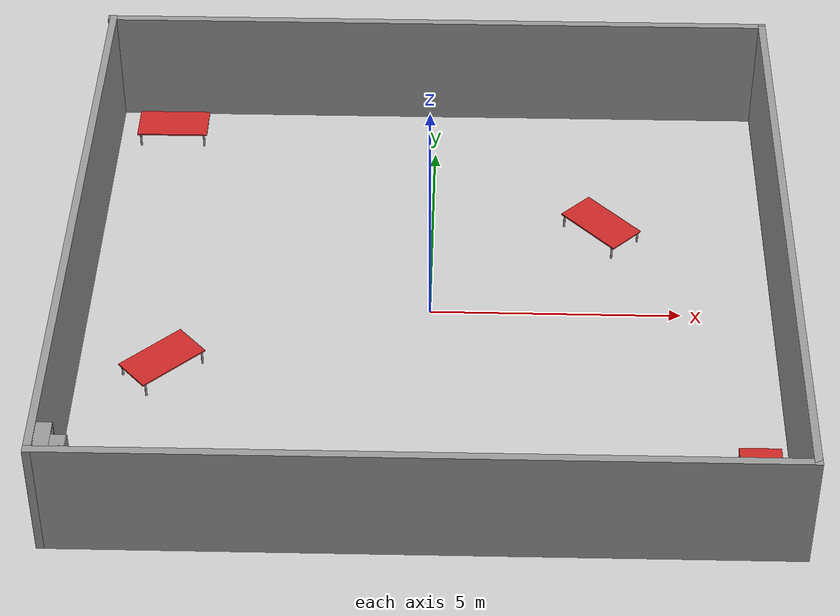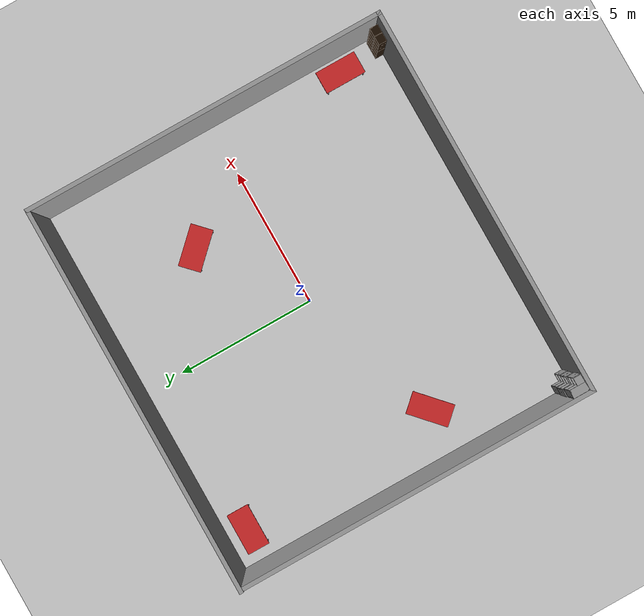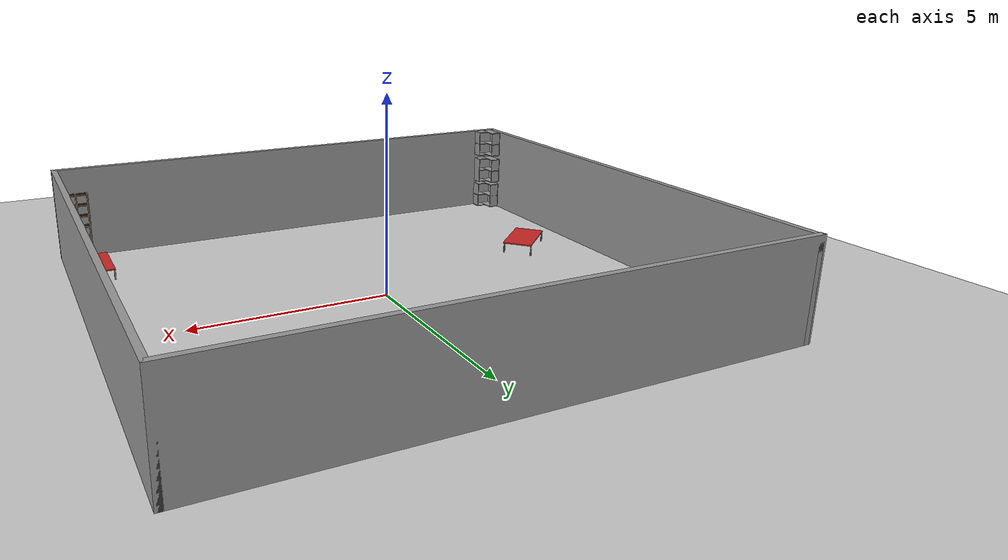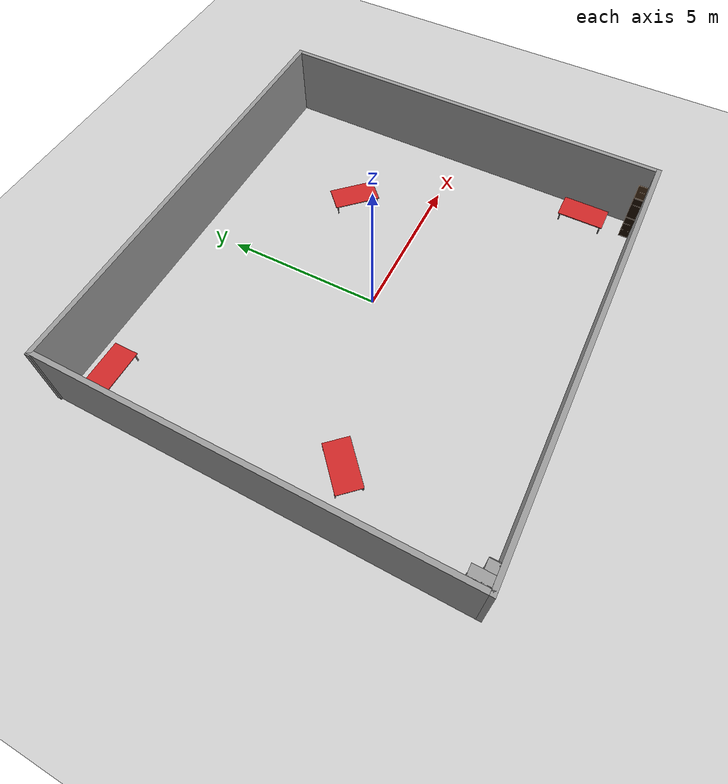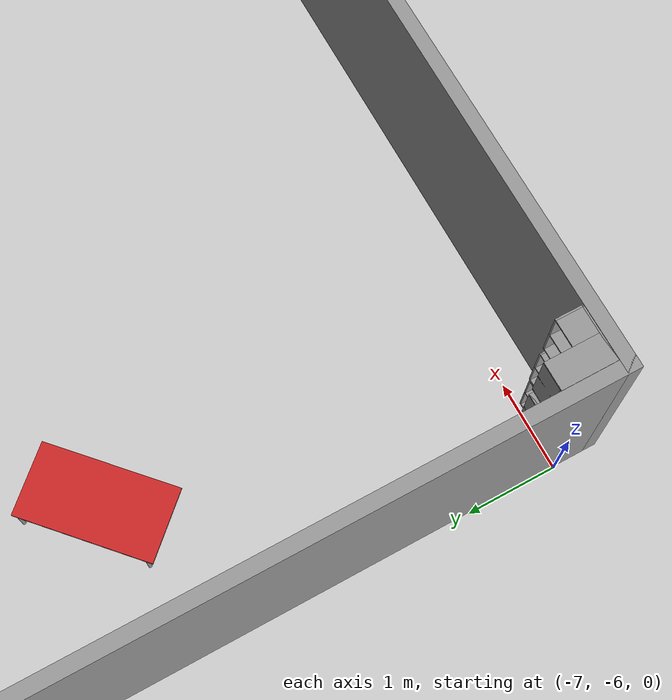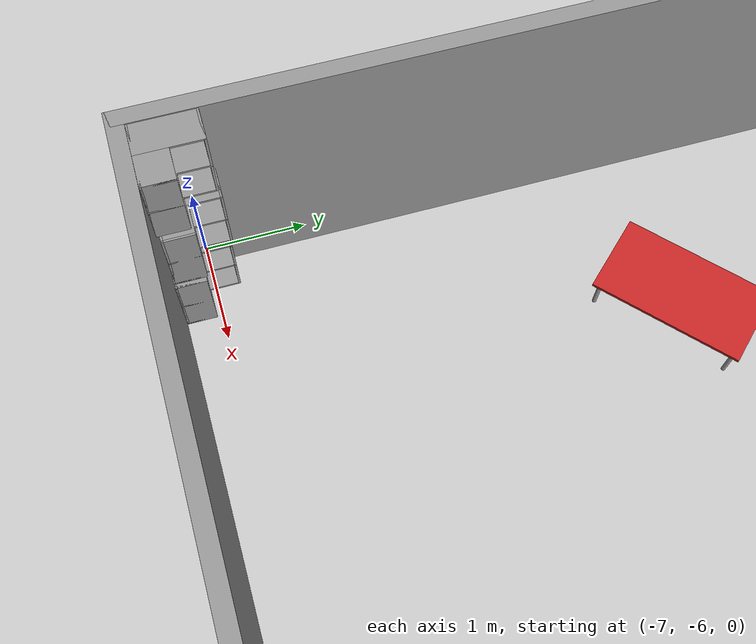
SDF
<sdf version="1.6">
 <world name="Own Room">
  <light name="sun" type="directional">
   <pose>0 0 10 0 -0 0</pose>
   <diffuse>0.8 0.8 0.8 1</diffuse>
   <specular>0.2 0.2 0.2 1</specular>
   <attenuation>
    <range>1000</range>
    <constant>0.9</constant>
    <linear>0.01</linear>
    <quadratic>0.001</quadratic>
   </attenuation>
   <direction>-0.5 0.1 -0.9</direction>
  </light>
  <model name="ground_plane">
   <static>1</static>
   <link name="link">
    <collision name="collision">
     <geometry><plane><normal>0 0 1</normal><size>100 100</size></plane></geometry>
     <surface>
      <contact><collide_bitmask>65535</collide_bitmask></contact>
      <friction><ode><mu>100</mu><mu2>50</mu2></ode></friction>
     </surface>
    </collision>
    <visual name="visual">
     <cast_shadows>0</cast_shadows>
     <geometry><plane><normal>0 0 1</normal><size>100 100</size></plane></geometry>
     <material>
      <script><uri>file://media/materials/scripts/gazebo.material</uri><name>Gazebo/Grey</name></script>
     </material>
    </visual>
   </link>
  </model>
  <gravity>0 0 -9.8</gravity>
  <magnetic_field>6e-06 2.3e-05 -4.2e-05</magnetic_field>
  <atmosphere type="adiabatic"/>
  <physics name="default_physics" default="0" type="ode">
   <max_step_size>0.001</max_step_size>
   <real_time_factor>1</real_time_factor>
   <real_time_update_rate>1000</real_time_update_rate>
  </physics>
  <scene><ambient>0.4 0.4 0.4 1</ambient><background>0.7 0.7 0.7 1</background><shadows>1</shadows></scene>
  <spherical_coordinates>
   <surface_model>EARTH_WGS84</surface_model>
   <latitude_deg>0</latitude_deg>
   <longitude_deg>0</longitude_deg>
   <elevation>0</elevation>
   <heading_deg>0</heading_deg>
  </spherical_coordinates>
  <model name="Room">
   <pose>-0.022602 0.001659 0 0 -0 0</pose>
   <link name="Wall_1">
    <collision name="Wall_1_Collision">
     <geometry><box><size>13 0.15 2.5</size></box></geometry>
     <pose>0 0 1.25 0 -0 0</pose>
    </collision>
    <visual name="Wall_1_Visual">
     <pose>0 0 1.25 0 -0 0</pose>
     <geometry><box><size>13 0.15 2.5</size></box></geometry>
     <material>
      <script><uri>file://media/materials/scripts/gazebo.material</uri><name>Gazebo/Grey</name></script>
      <ambient>0.333333 0.341176 0.32549 1</ambient>
     </material>
     <meta><layer>0</layer></meta>
    </visual>
    <pose>-6.88982 -0 0 0 -0 1.5708</pose>
   </link>
   <link name="Wall_2">
    <collision name="Wall_2_Collision">
     <geometry><box><size>14 0.15 2.5</size></box></geometry>
     <pose>0 0 1.25 0 -0 0</pose>
    </collision>
    <visual name="Wall_2_Visual">
     <pose>0 0 1.25 0 -0 0</pose>
     <geometry><box><size>14 0.15 2.5</size></box></geometry>
     <material>
      <script><uri>file://media/materials/scripts/gazebo.material</uri><name>Gazebo/Grey</name></script>
      <ambient>0.333333 0.341176 0.32549 1</ambient>
     </material>
     <meta><layer>0</layer></meta>
    </visual>
    <pose>-0 6.425 0 0 -0 0</pose>
   </link>
   <link name="Wall_4">
    <collision name="Wall_4_Collision">
     <geometry><box><size>13 0.15 2.5</size></box></geometry>
     <pose>0 0 1.25 0 -0 0</pose>
    </collision>
    <visual name="Wall_4_Visual">
     <pose>0 0 1.25 0 -0 0</pose>
     <geometry><box><size>13 0.15 2.5</size></box></geometry>
     <material>
      <script><uri>file://media/materials/scripts/gazebo.material</uri><name>Gazebo/Grey</name></script>
      <ambient>0.333333 0.341176 0.32549 1</ambient>
     </material>
     <meta><layer>0</layer></meta>
    </visual>
    <pose>6.925 -0 0 0 -0 -1.5708</pose>
   </link>
   <link name="Wall_5">
    <collision name="Wall_5_Collision">
     <geometry><box><size>13.9648 0.15 2.5</size></box></geometry>
     <pose>0 0 1.25 0 -0 0</pose>
    </collision>
    <visual name="Wall_5_Visual">
     <pose>0 0 1.25 0 -0 0</pose>
     <geometry><box><size>13.9648 0.15 2.5</size></box></geometry>
     <material>
      <script><uri>file://media/materials/scripts/gazebo.material</uri><name>Gazebo/Grey</name></script>
      <ambient>0.333333 0.341176 0.32549 1</ambient>
     </material>
     <meta><layer>0</layer></meta>
    </visual>
    <pose>0.017589 -6.425 0 0 -0 3.14159</pose>
   </link>
   <static>1</static>
  </model>
  <model name="table">
   <link name="link">
    <inertial>
     <mass>1</mass>
     <inertia><ixx>1</ixx><ixy>0</ixy><ixz>0</ixz><iyy>1</iyy><iyz>0</iyz><izz>1</izz></inertia>
    </inertial>
    <visual name="front_right_leg">
     <pose>0.68 -0.38 0.15 0 -0 0</pose>
     <geometry><cylinder><radius>0.02</radius><length>0.3</length></cylinder></geometry>
     <material>
      <script><uri>file://media/materials/scripts/gazebo.material</uri><name>Gazebo/Grey</name></script>
      <shader type="pixel"><normal_map>__default__</normal_map></shader>
      <ambient>0.3 0.3 0.3 1</ambient>
      <diffuse>0.7 0.7 0.7 1</diffuse>
      <specular>0.01 0.01 0.01 1</specular>
      <emissive>0 0 0 1</emissive>
     </material>
    </visual>
    <visual name="back_left_leg">
     <pose>-0.68 0.38 0.15 0 -0 0</pose>
     <geometry><cylinder><radius>0.02</radius><length>0.3</length></cylinder></geometry>
     <material>
      <script><uri>file://media/materials/scripts/gazebo.material</uri><name>Gazebo/Grey</name></script>
      <shader type="pixel"><normal_map>__default__</normal_map></shader>
      <ambient>0.3 0.3 0.3 1</ambient>
      <diffuse>0.7 0.7 0.7 1</diffuse>
      <specular>0.01 0.01 0.01 1</specular>
      <emissive>0 0 0 1</emissive>
     </material>
    </visual>
    <visual name="front_left_leg">
     <pose>0.68 0.38 0.15 0 -0 0</pose>
     <geometry><cylinder><radius>0.02</radius><length>0.3</length></cylinder></geometry>
     <material>
      <script><uri>file://media/materials/scripts/gazebo.material</uri><name>Gazebo/Grey</name></script>
      <shader type="pixel"><normal_map>__default__</normal_map></shader>
      <ambient>0.3 0.3 0.3 1</ambient>
      <diffuse>0.7 0.7 0.7 1</diffuse>
      <specular>0.01 0.01 0.01 1</specular>
      <emissive>0 0 0 1</emissive>
     </material>
    </visual>
    <visual name="visual1">
     <pose>0 0 0.3 0 -0 0</pose>
     <geometry><box><size>1.5 0.8 0.03</size></box></geometry>
     <material>
      <script><uri>file://media/materials/scripts/gazebo.material</uri><name>Gazebo/Red</name></script>
      <shader type="vertex"><normal_map>__default__</normal_map></shader>
      <ambient>1 0 0 1</ambient>
      <diffuse>1 0 0 1</diffuse>
      <specular>0.2 0 0 1</specular>
      <emissive>0 0 0 1</emissive>
      <lighting>1</lighting>
     </material>
    </visual>
    <visual name="back_right_leg">
     <pose>-0.68 -0.38 0.15 0 -0 0</pose>
     <geometry><cylinder><radius>0.02</radius><length>0.3</length></cylinder></geometry>
     <material>
      <script><uri>file://media/materials/scripts/gazebo.material</uri><name>Gazebo/Grey</name></script>
      <shader type="pixel"><normal_map>__default__</normal_map></shader>
      <ambient>0.3 0.3 0.3 1</ambient>
      <diffuse>0.7 0.7 0.7 1</diffuse>
      <specular>0.01 0.01 0.01 1</specular>
      <emissive>0 0 0 1</emissive>
     </material>
    </visual>
    <collision name="front_left_leg">
     <pose>0.68 0.38 0.15 0 -0 0</pose>
     <geometry><cylinder><radius>0.02</radius><length>0.3</length></cylinder></geometry>
     <surface>
      <friction>
       <ode><mu>1</mu><mu2>1</mu2><fdir1>0 0 0</fdir1><slip1>0</slip1><slip2>0</slip2></ode>
       <torsional>
        <coefficient>1</coefficient>
        <patch_radius>0</patch_radius>
        <surface_radius>0</surface_radius>
        <use_patch_radius>1</use_patch_radius>
        <ode><slip>0</slip></ode>
       </torsional>
      </friction>
      <bounce><restitution_coefficient>0</restitution_coefficient><threshold>1e+06</threshold></bounce>
      <contact>
       <collide_without_contact>0</collide_without_contact>
       <collide_without_contact_bitmask>1</collide_without_contact_bitmask>
       <collide_bitmask>1</collide_bitmask>
       <ode>
        <soft_cfm>0</soft_cfm>
        <soft_erp>0.2</soft_erp>
        <kp>1e+13</kp>
        <kd>1</kd>
        <max_vel>0.01</max_vel>
        <min_depth>0</min_depth>
       </ode>
       <bullet>
        <split_impulse>1</split_impulse>
        <split_impulse_penetration_threshold>-0.01</split_impulse_penetration_threshold>
        <soft_cfm>0</soft_cfm>
        <soft_erp>0.2</soft_erp>
        <kp>1e+13</kp>
        <kd>1</kd>
       </bullet>
      </contact>
     </surface>
    </collision>
    <collision name="back_right_leg">
     <pose>-0.68 -0.38 0.15 0 -0 0</pose>
     <geometry><cylinder><radius>0.02</radius><length>0.3</length></cylinder></geometry>
     <surface>
      <friction>
       <ode><mu>1</mu><mu2>1</mu2><fdir1>0 0 0</fdir1><slip1>0</slip1><slip2>0</slip2></ode>
       <torsional>
        <coefficient>1</coefficient>
        <patch_radius>0</patch_radius>
        <surface_radius>0</surface_radius>
        <use_patch_radius>1</use_patch_radius>
        <ode><slip>0</slip></ode>
       </torsional>
      </friction>
      <bounce><restitution_coefficient>0</restitution_coefficient><threshold>1e+06</threshold></bounce>
      <contact>
       <collide_without_contact>0</collide_without_contact>
       <collide_without_contact_bitmask>1</collide_without_contact_bitmask>
       <collide_bitmask>1</collide_bitmask>
       <ode>
        <soft_cfm>0</soft_cfm>
        <soft_erp>0.2</soft_erp>
        <kp>1e+13</kp>
        <kd>1</kd>
        <max_vel>0.01</max_vel>
        <min_depth>0</min_depth>
       </ode>
       <bullet>
        <split_impulse>1</split_impulse>
        <split_impulse_penetration_threshold>-0.01</split_impulse_penetration_threshold>
        <soft_cfm>0</soft_cfm>
        <soft_erp>0.2</soft_erp>
        <kp>1e+13</kp>
        <kd>1</kd>
       </bullet>
      </contact>
     </surface>
    </collision>
    <collision name="back_left_leg">
     <pose>-0.68 0.38 0.15 0 -0 0</pose>
     <geometry><cylinder><radius>0.02</radius><length>0.3</length></cylinder></geometry>
     <surface>
      <friction>
       <ode><mu>1</mu><mu2>1</mu2><fdir1>0 0 0</fdir1><slip1>0</slip1><slip2>0</slip2></ode>
       <torsional>
        <coefficient>1</coefficient>
        <patch_radius>0</patch_radius>
        <surface_radius>0</surface_radius>
        <use_patch_radius>1</use_patch_radius>
        <ode><slip>0</slip></ode>
       </torsional>
      </friction>
      <bounce><restitution_coefficient>0</restitution_coefficient><threshold>1e+06</threshold></bounce>
      <contact>
       <collide_without_contact>0</collide_without_contact>
       <collide_without_contact_bitmask>1</collide_without_contact_bitmask>
       <collide_bitmask>1</collide_bitmask>
       <ode>
        <soft_cfm>0</soft_cfm>
        <soft_erp>0.2</soft_erp>
        <kp>1e+13</kp>
        <kd>1</kd>
        <max_vel>0.01</max_vel>
        <min_depth>0</min_depth>
       </ode>
       <bullet>
        <split_impulse>1</split_impulse>
        <split_impulse_penetration_threshold>-0.01</split_impulse_penetration_threshold>
        <soft_cfm>0</soft_cfm>
        <soft_erp>0.2</soft_erp>
        <kp>1e+13</kp>
        <kd>1</kd>
       </bullet>
      </contact>
     </surface>
    </collision>
    <collision name="surface">
     <pose>0 0 0.3 0 -0 0</pose>
     <geometry><box><size>1.5 0.8 0.03</size></box></geometry>
     <surface>
      <friction>
       <ode><mu>0.6</mu><mu2>0.6</mu2><fdir1>0 0 0</fdir1><slip1>0</slip1><slip2>0</slip2></ode>
       <torsional>
        <coefficient>1</coefficient>
        <patch_radius>0</patch_radius>
        <surface_radius>0</surface_radius>
        <use_patch_radius>1</use_patch_radius>
        <ode><slip>0</slip></ode>
       </torsional>
      </friction>
      <bounce><restitution_coefficient>0</restitution_coefficient><threshold>1e+06</threshold></bounce>
      <contact>
       <collide_without_contact>0</collide_without_contact>
       <collide_without_contact_bitmask>1</collide_without_contact_bitmask>
       <collide_bitmask>1</collide_bitmask>
       <ode>
        <soft_cfm>0</soft_cfm>
        <soft_erp>0.2</soft_erp>
        <kp>1e+13</kp>
        <kd>1</kd>
        <max_vel>0.01</max_vel>
        <min_depth>0</min_depth>
       </ode>
       <bullet>
        <split_impulse>1</split_impulse>
        <split_impulse_penetration_threshold>-0.01</split_impulse_penetration_threshold>
        <soft_cfm>0</soft_cfm>
        <soft_erp>0.2</soft_erp>
        <kp>1e+13</kp>
        <kd>1</kd>
       </bullet>
      </contact>
     </surface>
    </collision>
    <collision name="front_right_leg">
     <pose>0.68 -0.38 0.15 0 -0 0</pose>
     <geometry><cylinder><radius>0.02</radius><length>0.3</length></cylinder></geometry>
     <surface>
      <friction>
       <ode><mu>1</mu><mu2>1</mu2><fdir1>0 0 0</fdir1><slip1>0</slip1><slip2>0</slip2></ode>
       <torsional>
        <coefficient>1</coefficient>
        <patch_radius>0</patch_radius>
        <surface_radius>0</surface_radius>
        <use_patch_radius>1</use_patch_radius>
        <ode><slip>0</slip></ode>
       </torsional>
      </friction>
      <bounce><restitution_coefficient>0</restitution_coefficient><threshold>1e+06</threshold></bounce>
      <contact>
       <collide_without_contact>0</collide_without_contact>
       <collide_without_contact_bitmask>1</collide_without_contact_bitmask>
       <collide_bitmask>1</collide_bitmask>
       <ode>
        <soft_cfm>0</soft_cfm>
        <soft_erp>0.2</soft_erp>
        <kp>1e+13</kp>
        <kd>1</kd>
        <max_vel>0.01</max_vel>
        <min_depth>0</min_depth>
       </ode>
       <bullet>
        <split_impulse>1</split_impulse>
        <split_impulse_penetration_threshold>-0.01</split_impulse_penetration_threshold>
        <soft_cfm>0</soft_cfm>
        <soft_erp>0.2</soft_erp>
        <kp>1e+13</kp>
        <kd>1</kd>
       </bullet>
      </contact>
     </surface>
    </collision>
   </link>
   <static>1</static>
   <pose>-5.68589 5.59801 0 0 -0 0</pose>
  </model>
  <model name="table_0">
   <link name="link">
    <inertial>
     <mass>1</mass>
     <inertia><ixx>1</ixx><ixy>0</ixy><ixz>0</ixz><iyy>1</iyy><iyz>0</iyz><izz>1</izz></inertia>
    </inertial>
    <visual name="front_right_leg">
     <pose>0.68 -0.38 0.15 0 -0 0</pose>
     <geometry><cylinder><radius>0.02</radius><length>0.3</length></cylinder></geometry>
     <material>
      <script><uri>file://media/materials/scripts/gazebo.material</uri><name>Gazebo/Grey</name></script>
      <shader type="pixel"><normal_map>__default__</normal_map></shader>
      <ambient>0.3 0.3 0.3 1</ambient>
      <diffuse>0.7 0.7 0.7 1</diffuse>
      <specular>0.01 0.01 0.01 1</specular>
      <emissive>0 0 0 1</emissive>
     </material>
    </visual>
    <visual name="back_left_leg">
     <pose>-0.68 0.38 0.15 0 -0 0</pose>
     <geometry><cylinder><radius>0.02</radius><length>0.3</length></cylinder></geometry>
     <material>
      <script><uri>file://media/materials/scripts/gazebo.material</uri><name>Gazebo/Grey</name></script>
      <shader type="pixel"><normal_map>__default__</normal_map></shader>
      <ambient>0.3 0.3 0.3 1</ambient>
      <diffuse>0.7 0.7 0.7 1</diffuse>
      <specular>0.01 0.01 0.01 1</specular>
      <emissive>0 0 0 1</emissive>
     </material>
    </visual>
    <visual name="front_left_leg">
     <pose>0.68 0.38 0.15 0 -0 0</pose>
     <geometry><cylinder><radius>0.02</radius><length>0.3</length></cylinder></geometry>
     <material>
      <script><uri>file://media/materials/scripts/gazebo.material</uri><name>Gazebo/Grey</name></script>
      <shader type="pixel"><normal_map>__default__</normal_map></shader>
      <ambient>0.3 0.3 0.3 1</ambient>
      <diffuse>0.7 0.7 0.7 1</diffuse>
      <specular>0.01 0.01 0.01 1</specular>
      <emissive>0 0 0 1</emissive>
     </material>
    </visual>
    <visual name="visual1">
     <pose>0 0 0.3 0 -0 0</pose>
     <geometry><box><size>1.5 0.8 0.03</size></box></geometry>
     <material>
      <script><uri>file://media/materials/scripts/gazebo.material</uri><name>Gazebo/Red</name></script>
      <shader type="vertex"><normal_map>__default__</normal_map></shader>
      <ambient>1 0 0 1</ambient>
      <diffuse>1 0 0 1</diffuse>
      <specular>0.2 0 0 1</specular>
      <emissive>0 0 0 1</emissive>
      <lighting>1</lighting>
     </material>
    </visual>
    <visual name="back_right_leg">
     <pose>-0.68 -0.38 0.15 0 -0 0</pose>
     <geometry><cylinder><radius>0.02</radius><length>0.3</length></cylinder></geometry>
     <material>
      <script><uri>file://media/materials/scripts/gazebo.material</uri><name>Gazebo/Grey</name></script>
      <shader type="pixel"><normal_map>__default__</normal_map></shader>
      <ambient>0.3 0.3 0.3 1</ambient>
      <diffuse>0.7 0.7 0.7 1</diffuse>
      <specular>0.01 0.01 0.01 1</specular>
      <emissive>0 0 0 1</emissive>
     </material>
    </visual>
    <collision name="front_left_leg">
     <pose>0.68 0.38 0.15 0 -0 0</pose>
     <geometry><cylinder><radius>0.02</radius><length>0.3</length></cylinder></geometry>
     <surface>
      <friction>
       <ode><mu>1</mu><mu2>1</mu2><fdir1>0 0 0</fdir1><slip1>0</slip1><slip2>0</slip2></ode>
       <torsional>
        <coefficient>1</coefficient>
        <patch_radius>0</patch_radius>
        <surface_radius>0</surface_radius>
        <use_patch_radius>1</use_patch_radius>
        <ode><slip>0</slip></ode>
       </torsional>
      </friction>
      <bounce><restitution_coefficient>0</restitution_coefficient><threshold>1e+06</threshold></bounce>
      <contact>
       <collide_without_contact>0</collide_without_contact>
       <collide_without_contact_bitmask>1</collide_without_contact_bitmask>
       <collide_bitmask>1</collide_bitmask>
       <ode>
        <soft_cfm>0</soft_cfm>
        <soft_erp>0.2</soft_erp>
        <kp>1e+13</kp>
        <kd>1</kd>
        <max_vel>0.01</max_vel>
        <min_depth>0</min_depth>
       </ode>
       <bullet>
        <split_impulse>1</split_impulse>
        <split_impulse_penetration_threshold>-0.01</split_impulse_penetration_threshold>
        <soft_cfm>0</soft_cfm>
        <soft_erp>0.2</soft_erp>
        <kp>1e+13</kp>
        <kd>1</kd>
       </bullet>
      </contact>
     </surface>
    </collision>
    <collision name="back_right_leg">
     <pose>-0.68 -0.38 0.15 0 -0 0</pose>
     <geometry><cylinder><radius>0.02</radius><length>0.3</length></cylinder></geometry>
     <surface>
      <friction>
       <ode><mu>1</mu><mu2>1</mu2><fdir1>0 0 0</fdir1><slip1>0</slip1><slip2>0</slip2></ode>
       <torsional>
        <coefficient>1</coefficient>
        <patch_radius>0</patch_radius>
        <surface_radius>0</surface_radius>
        <use_patch_radius>1</use_patch_radius>
        <ode><slip>0</slip></ode>
       </torsional>
      </friction>
      <bounce><restitution_coefficient>0</restitution_coefficient><threshold>1e+06</threshold></bounce>
      <contact>
       <collide_without_contact>0</collide_without_contact>
       <collide_without_contact_bitmask>1</collide_without_contact_bitmask>
       <collide_bitmask>1</collide_bitmask>
       <ode>
        <soft_cfm>0</soft_cfm>
        <soft_erp>0.2</soft_erp>
        <kp>1e+13</kp>
        <kd>1</kd>
        <max_vel>0.01</max_vel>
        <min_depth>0</min_depth>
       </ode>
       <bullet>
        <split_impulse>1</split_impulse>
        <split_impulse_penetration_threshold>-0.01</split_impulse_penetration_threshold>
        <soft_cfm>0</soft_cfm>
        <soft_erp>0.2</soft_erp>
        <kp>1e+13</kp>
        <kd>1</kd>
       </bullet>
      </contact>
     </surface>
    </collision>
    <collision name="back_left_leg">
     <pose>-0.68 0.38 0.15 0 -0 0</pose>
     <geometry><cylinder><radius>0.02</radius><length>0.3</length></cylinder></geometry>
     <surface>
      <friction>
       <ode><mu>1</mu><mu2>1</mu2><fdir1>0 0 0</fdir1><slip1>0</slip1><slip2>0</slip2></ode>
       <torsional>
        <coefficient>1</coefficient>
        <patch_radius>0</patch_radius>
        <surface_radius>0</surface_radius>
        <use_patch_radius>1</use_patch_radius>
        <ode><slip>0</slip></ode>
       </torsional>
      </friction>
      <bounce><restitution_coefficient>0</restitution_coefficient><threshold>1e+06</threshold></bounce>
      <contact>
       <collide_without_contact>0</collide_without_contact>
       <collide_without_contact_bitmask>1</collide_without_contact_bitmask>
       <collide_bitmask>1</collide_bitmask>
       <ode>
        <soft_cfm>0</soft_cfm>
        <soft_erp>0.2</soft_erp>
        <kp>1e+13</kp>
        <kd>1</kd>
        <max_vel>0.01</max_vel>
        <min_depth>0</min_depth>
       </ode>
       <bullet>
        <split_impulse>1</split_impulse>
        <split_impulse_penetration_threshold>-0.01</split_impulse_penetration_threshold>
        <soft_cfm>0</soft_cfm>
        <soft_erp>0.2</soft_erp>
        <kp>1e+13</kp>
        <kd>1</kd>
       </bullet>
      </contact>
     </surface>
    </collision>
    <collision name="surface">
     <pose>0 0 0.3 0 -0 0</pose>
     <geometry><box><size>1.5 0.8 0.03</size></box></geometry>
     <surface>
      <friction>
       <ode><mu>0.6</mu><mu2>0.6</mu2><fdir1>0 0 0</fdir1><slip1>0</slip1><slip2>0</slip2></ode>
       <torsional>
        <coefficient>1</coefficient>
        <patch_radius>0</patch_radius>
        <surface_radius>0</surface_radius>
        <use_patch_radius>1</use_patch_radius>
        <ode><slip>0</slip></ode>
       </torsional>
      </friction>
      <bounce><restitution_coefficient>0</restitution_coefficient><threshold>1e+06</threshold></bounce>
      <contact>
       <collide_without_contact>0</collide_without_contact>
       <collide_without_contact_bitmask>1</collide_without_contact_bitmask>
       <collide_bitmask>1</collide_bitmask>
       <ode>
        <soft_cfm>0</soft_cfm>
        <soft_erp>0.2</soft_erp>
        <kp>1e+13</kp>
        <kd>1</kd>
        <max_vel>0.01</max_vel>
        <min_depth>0</min_depth>
       </ode>
       <bullet>
        <split_impulse>1</split_impulse>
        <split_impulse_penetration_threshold>-0.01</split_impulse_penetration_threshold>
        <soft_cfm>0</soft_cfm>
        <soft_erp>0.2</soft_erp>
        <kp>1e+13</kp>
        <kd>1</kd>
       </bullet>
      </contact>
     </surface>
    </collision>
    <collision name="front_right_leg">
     <pose>0.68 -0.38 0.15 0 -0 0</pose>
     <geometry><cylinder><radius>0.02</radius><length>0.3</length></cylinder></geometry>
     <surface>
      <friction>
       <ode><mu>1</mu><mu2>1</mu2><fdir1>0 0 0</fdir1><slip1>0</slip1><slip2>0</slip2></ode>
       <torsional>
        <coefficient>1</coefficient>
        <patch_radius>0</patch_radius>
        <surface_radius>0</surface_radius>
        <use_patch_radius>1</use_patch_radius>
        <ode><slip>0</slip></ode>
       </torsional>
      </friction>
      <bounce><restitution_coefficient>0</restitution_coefficient><threshold>1e+06</threshold></bounce>
      <contact>
       <collide_without_contact>0</collide_without_contact>
       <collide_without_contact_bitmask>1</collide_without_contact_bitmask>
       <collide_bitmask>1</collide_bitmask>
       <ode>
        <soft_cfm>0</soft_cfm>
        <soft_erp>0.2</soft_erp>
        <kp>1e+13</kp>
        <kd>1</kd>
        <max_vel>0.01</max_vel>
        <min_depth>0</min_depth>
       </ode>
       <bullet>
        <split_impulse>1</split_impulse>
        <split_impulse_penetration_threshold>-0.01</split_impulse_penetration_threshold>
        <soft_cfm>0</soft_cfm>
        <soft_erp>0.2</soft_erp>
        <kp>1e+13</kp>
        <kd>1</kd>
       </bullet>
      </contact>
     </surface>
    </collision>
   </link>
   <static>1</static>
   <pose>6.26711 -4.72705 0 0 0 -1.56938</pose>
  </model>
  <model name="table_1">
   <link name="link">
    <inertial>
     <mass>1</mass>
     <inertia><ixx>1</ixx><ixy>0</ixy><ixz>0</ixz><iyy>1</iyy><iyz>0</iyz><izz>1</izz></inertia>
    </inertial>
    <visual name="front_right_leg">
     <pose>0.68 -0.38 0.15 0 -0 0</pose>
     <geometry><cylinder><radius>0.02</radius><length>0.3</length></cylinder></geometry>
     <material>
      <script><uri>file://media/materials/scripts/gazebo.material</uri><name>Gazebo/Grey</name></script>
      <shader type="pixel"><normal_map>__default__</normal_map></shader>
      <ambient>0.3 0.3 0.3 1</ambient>
      <diffuse>0.7 0.7 0.7 1</diffuse>
      <specular>0.01 0.01 0.01 1</specular>
      <emissive>0 0 0 1</emissive>
     </material>
    </visual>
    <visual name="back_left_leg">
     <pose>-0.68 0.38 0.15 0 -0 0</pose>
     <geometry><cylinder><radius>0.02</radius><length>0.3</length></cylinder></geometry>
     <material>
      <script><uri>file://media/materials/scripts/gazebo.material</uri><name>Gazebo/Grey</name></script>
      <shader type="pixel"><normal_map>__default__</normal_map></shader>
      <ambient>0.3 0.3 0.3 1</ambient>
      <diffuse>0.7 0.7 0.7 1</diffuse>
      <specular>0.01 0.01 0.01 1</specular>
      <emissive>0 0 0 1</emissive>
     </material>
    </visual>
    <visual name="front_left_leg">
     <pose>0.68 0.38 0.15 0 -0 0</pose>
     <geometry><cylinder><radius>0.02</radius><length>0.3</length></cylinder></geometry>
     <material>
      <script><uri>file://media/materials/scripts/gazebo.material</uri><name>Gazebo/Grey</name></script>
      <shader type="pixel"><normal_map>__default__</normal_map></shader>
      <ambient>0.3 0.3 0.3 1</ambient>
      <diffuse>0.7 0.7 0.7 1</diffuse>
      <specular>0.01 0.01 0.01 1</specular>
      <emissive>0 0 0 1</emissive>
     </material>
    </visual>
    <visual name="visual1">
     <pose>0 0 0.3 0 -0 0</pose>
     <geometry><box><size>1.5 0.8 0.03</size></box></geometry>
     <material>
      <script><uri>file://media/materials/scripts/gazebo.material</uri><name>Gazebo/Red</name></script>
      <shader type="vertex"><normal_map>__default__</normal_map></shader>
      <ambient>1 0 0 1</ambient>
      <diffuse>1 0 0 1</diffuse>
      <specular>0.2 0 0 1</specular>
      <emissive>0 0 0 1</emissive>
      <lighting>1</lighting>
     </material>
    </visual>
    <visual name="back_right_leg">
     <pose>-0.68 -0.38 0.15 0 -0 0</pose>
     <geometry><cylinder><radius>0.02</radius><length>0.3</length></cylinder></geometry>
     <material>
      <script><uri>file://media/materials/scripts/gazebo.material</uri><name>Gazebo/Grey</name></script>
      <shader type="pixel"><normal_map>__default__</normal_map></shader>
      <ambient>0.3 0.3 0.3 1</ambient>
      <diffuse>0.7 0.7 0.7 1</diffuse>
      <specular>0.01 0.01 0.01 1</specular>
      <emissive>0 0 0 1</emissive>
     </material>
    </visual>
    <collision name="front_left_leg">
     <pose>0.68 0.38 0.15 0 -0 0</pose>
     <geometry><cylinder><radius>0.02</radius><length>0.3</length></cylinder></geometry>
     <surface>
      <friction>
       <ode><mu>1</mu><mu2>1</mu2><fdir1>0 0 0</fdir1><slip1>0</slip1><slip2>0</slip2></ode>
       <torsional>
        <coefficient>1</coefficient>
        <patch_radius>0</patch_radius>
        <surface_radius>0</surface_radius>
        <use_patch_radius>1</use_patch_radius>
        <ode><slip>0</slip></ode>
       </torsional>
      </friction>
      <bounce><restitution_coefficient>0</restitution_coefficient><threshold>1e+06</threshold></bounce>
      <contact>
       <collide_without_contact>0</collide_without_contact>
       <collide_without_contact_bitmask>1</collide_without_contact_bitmask>
       <collide_bitmask>1</collide_bitmask>
       <ode>
        <soft_cfm>0</soft_cfm>
        <soft_erp>0.2</soft_erp>
        <kp>1e+13</kp>
        <kd>1</kd>
        <max_vel>0.01</max_vel>
        <min_depth>0</min_depth>
       </ode>
       <bullet>
        <split_impulse>1</split_impulse>
        <split_impulse_penetration_threshold>-0.01</split_impulse_penetration_threshold>
        <soft_cfm>0</soft_cfm>
        <soft_erp>0.2</soft_erp>
        <kp>1e+13</kp>
        <kd>1</kd>
       </bullet>
      </contact>
     </surface>
    </collision>
    <collision name="back_right_leg">
     <pose>-0.68 -0.38 0.15 0 -0 0</pose>
     <geometry><cylinder><radius>0.02</radius><length>0.3</length></cylinder></geometry>
     <surface>
      <friction>
       <ode><mu>1</mu><mu2>1</mu2><fdir1>0 0 0</fdir1><slip1>0</slip1><slip2>0</slip2></ode>
       <torsional>
        <coefficient>1</coefficient>
        <patch_radius>0</patch_radius>
        <surface_radius>0</surface_radius>
        <use_patch_radius>1</use_patch_radius>
        <ode><slip>0</slip></ode>
       </torsional>
      </friction>
      <bounce><restitution_coefficient>0</restitution_coefficient><threshold>1e+06</threshold></bounce>
      <contact>
       <collide_without_contact>0</collide_without_contact>
       <collide_without_contact_bitmask>1</collide_without_contact_bitmask>
       <collide_bitmask>1</collide_bitmask>
       <ode>
        <soft_cfm>0</soft_cfm>
        <soft_erp>0.2</soft_erp>
        <kp>1e+13</kp>
        <kd>1</kd>
        <max_vel>0.01</max_vel>
        <min_depth>0</min_depth>
       </ode>
       <bullet>
        <split_impulse>1</split_impulse>
        <split_impulse_penetration_threshold>-0.01</split_impulse_penetration_threshold>
        <soft_cfm>0</soft_cfm>
        <soft_erp>0.2</soft_erp>
        <kp>1e+13</kp>
        <kd>1</kd>
       </bullet>
      </contact>
     </surface>
    </collision>
    <collision name="back_left_leg">
     <pose>-0.68 0.38 0.15 0 -0 0</pose>
     <geometry><cylinder><radius>0.02</radius><length>0.3</length></cylinder></geometry>
     <surface>
      <friction>
       <ode><mu>1</mu><mu2>1</mu2><fdir1>0 0 0</fdir1><slip1>0</slip1><slip2>0</slip2></ode>
       <torsional>
        <coefficient>1</coefficient>
        <patch_radius>0</patch_radius>
        <surface_radius>0</surface_radius>
        <use_patch_radius>1</use_patch_radius>
        <ode><slip>0</slip></ode>
       </torsional>
      </friction>
      <bounce><restitution_coefficient>0</restitution_coefficient><threshold>1e+06</threshold></bounce>
      <contact>
       <collide_without_contact>0</collide_without_contact>
       <collide_without_contact_bitmask>1</collide_without_contact_bitmask>
       <collide_bitmask>1</collide_bitmask>
       <ode>
        <soft_cfm>0</soft_cfm>
        <soft_erp>0.2</soft_erp>
        <kp>1e+13</kp>
        <kd>1</kd>
        <max_vel>0.01</max_vel>
        <min_depth>0</min_depth>
       </ode>
       <bullet>
        <split_impulse>1</split_impulse>
        <split_impulse_penetration_threshold>-0.01</split_impulse_penetration_threshold>
        <soft_cfm>0</soft_cfm>
        <soft_erp>0.2</soft_erp>
        <kp>1e+13</kp>
        <kd>1</kd>
       </bullet>
      </contact>
     </surface>
    </collision>
    <collision name="surface">
     <pose>0 0 0.3 0 -0 0</pose>
     <geometry><box><size>1.5 0.8 0.03</size></box></geometry>
     <surface>
      <friction>
       <ode><mu>0.6</mu><mu2>0.6</mu2><fdir1>0 0 0</fdir1><slip1>0</slip1><slip2>0</slip2></ode>
       <torsional>
        <coefficient>1</coefficient>
        <patch_radius>0</patch_radius>
        <surface_radius>0</surface_radius>
        <use_patch_radius>1</use_patch_radius>
        <ode><slip>0</slip></ode>
       </torsional>
      </friction>
      <bounce><restitution_coefficient>0</restitution_coefficient><threshold>1e+06</threshold></bounce>
      <contact>
       <collide_without_contact>0</collide_without_contact>
       <collide_without_contact_bitmask>1</collide_without_contact_bitmask>
       <collide_bitmask>1</collide_bitmask>
       <ode>
        <soft_cfm>0</soft_cfm>
        <soft_erp>0.2</soft_erp>
        <kp>1e+13</kp>
        <kd>1</kd>
        <max_vel>0.01</max_vel>
        <min_depth>0</min_depth>
       </ode>
       <bullet>
        <split_impulse>1</split_impulse>
        <split_impulse_penetration_threshold>-0.01</split_impulse_penetration_threshold>
        <soft_cfm>0</soft_cfm>
        <soft_erp>0.2</soft_erp>
        <kp>1e+13</kp>
        <kd>1</kd>
       </bullet>
      </contact>
     </surface>
    </collision>
    <collision name="front_right_leg">
     <pose>0.68 -0.38 0.15 0 -0 0</pose>
     <geometry><cylinder><radius>0.02</radius><length>0.3</length></cylinder></geometry>
     <surface>
      <friction>
       <ode><mu>1</mu><mu2>1</mu2><fdir1>0 0 0</fdir1><slip1>0</slip1><slip2>0</slip2></ode>
       <torsional>
        <coefficient>1</coefficient>
        <patch_radius>0</patch_radius>
        <surface_radius>0</surface_radius>
        <use_patch_radius>1</use_patch_radius>
        <ode><slip>0</slip></ode>
       </torsional>
      </friction>
      <bounce><restitution_coefficient>0</restitution_coefficient><threshold>1e+06</threshold></bounce>
      <contact>
       <collide_without_contact>0</collide_without_contact>
       <collide_without_contact_bitmask>1</collide_without_contact_bitmask>
       <collide_bitmask>1</collide_bitmask>
       <ode>
        <soft_cfm>0</soft_cfm>
        <soft_erp>0.2</soft_erp>
        <kp>1e+13</kp>
        <kd>1</kd>
        <max_vel>0.01</max_vel>
        <min_depth>0</min_depth>
       </ode>
       <bullet>
        <split_impulse>1</split_impulse>
        <split_impulse_penetration_threshold>-0.01</split_impulse_penetration_threshold>
        <soft_cfm>0</soft_cfm>
        <soft_erp>0.2</soft_erp>
        <kp>1e+13</kp>
        <kd>1</kd>
       </bullet>
      </contact>
     </surface>
    </collision>
   </link>
   <static>1</static>
   <pose>3.47543 2.47814 0 0 0 -0.802588</pose>
  </model>
  <model name="table_2">
   <link name="link">
    <inertial>
     <mass>1</mass>
     <inertia><ixx>1</ixx><ixy>0</ixy><ixz>0</ixz><iyy>1</iyy><iyz>0</iyz><izz>1</izz></inertia>
    </inertial>
    <visual name="front_right_leg">
     <pose>0.68 -0.38 0.15 0 -0 0</pose>
     <geometry><cylinder><radius>0.02</radius><length>0.3</length></cylinder></geometry>
     <material>
      <script><uri>file://media/materials/scripts/gazebo.material</uri><name>Gazebo/Grey</name></script>
      <shader type="pixel"><normal_map>__default__</normal_map></shader>
      <ambient>0.3 0.3 0.3 1</ambient>
      <diffuse>0.7 0.7 0.7 1</diffuse>
      <specular>0.01 0.01 0.01 1</specular>
      <emissive>0 0 0 1</emissive>
     </material>
    </visual>
    <visual name="back_left_leg">
     <pose>-0.68 0.38 0.15 0 -0 0</pose>
     <geometry><cylinder><radius>0.02</radius><length>0.3</length></cylinder></geometry>
     <material>
      <script><uri>file://media/materials/scripts/gazebo.material</uri><name>Gazebo/Grey</name></script>
      <shader type="pixel"><normal_map>__default__</normal_map></shader>
      <ambient>0.3 0.3 0.3 1</ambient>
      <diffuse>0.7 0.7 0.7 1</diffuse>
      <specular>0.01 0.01 0.01 1</specular>
      <emissive>0 0 0 1</emissive>
     </material>
    </visual>
    <visual name="front_left_leg">
     <pose>0.68 0.38 0.15 0 -0 0</pose>
     <geometry><cylinder><radius>0.02</radius><length>0.3</length></cylinder></geometry>
     <material>
      <script><uri>file://media/materials/scripts/gazebo.material</uri><name>Gazebo/Grey</name></script>
      <shader type="pixel"><normal_map>__default__</normal_map></shader>
      <ambient>0.3 0.3 0.3 1</ambient>
      <diffuse>0.7 0.7 0.7 1</diffuse>
      <specular>0.01 0.01 0.01 1</specular>
      <emissive>0 0 0 1</emissive>
     </material>
    </visual>
    <visual name="visual1">
     <pose>0 0 0.3 0 -0 0</pose>
     <geometry><box><size>1.5 0.8 0.03</size></box></geometry>
     <material>
      <script><uri>file://media/materials/scripts/gazebo.material</uri><name>Gazebo/Red</name></script>
      <shader type="vertex"><normal_map>__default__</normal_map></shader>
      <ambient>1 0 0 1</ambient>
      <diffuse>1 0 0 1</diffuse>
      <specular>0.2 0 0 1</specular>
      <emissive>0 0 0 1</emissive>
      <lighting>1</lighting>
     </material>
    </visual>
    <visual name="back_right_leg">
     <pose>-0.68 -0.38 0.15 0 -0 0</pose>
     <geometry><cylinder><radius>0.02</radius><length>0.3</length></cylinder></geometry>
     <material>
      <script><uri>file://media/materials/scripts/gazebo.material</uri><name>Gazebo/Grey</name></script>
      <shader type="pixel"><normal_map>__default__</normal_map></shader>
      <ambient>0.3 0.3 0.3 1</ambient>
      <diffuse>0.7 0.7 0.7 1</diffuse>
      <specular>0.01 0.01 0.01 1</specular>
      <emissive>0 0 0 1</emissive>
     </material>
    </visual>
    <collision name="front_left_leg">
     <pose>0.68 0.38 0.15 0 -0 0</pose>
     <geometry><cylinder><radius>0.02</radius><length>0.3</length></cylinder></geometry>
     <surface>
      <friction>
       <ode><mu>1</mu><mu2>1</mu2><fdir1>0 0 0</fdir1><slip1>0</slip1><slip2>0</slip2></ode>
       <torsional>
        <coefficient>1</coefficient>
        <patch_radius>0</patch_radius>
        <surface_radius>0</surface_radius>
        <use_patch_radius>1</use_patch_radius>
        <ode><slip>0</slip></ode>
       </torsional>
      </friction>
      <bounce><restitution_coefficient>0</restitution_coefficient><threshold>1e+06</threshold></bounce>
      <contact>
       <collide_without_contact>0</collide_without_contact>
       <collide_without_contact_bitmask>1</collide_without_contact_bitmask>
       <collide_bitmask>1</collide_bitmask>
       <ode>
        <soft_cfm>0</soft_cfm>
        <soft_erp>0.2</soft_erp>
        <kp>1e+13</kp>
        <kd>1</kd>
        <max_vel>0.01</max_vel>
        <min_depth>0</min_depth>
       </ode>
       <bullet>
        <split_impulse>1</split_impulse>
        <split_impulse_penetration_threshold>-0.01</split_impulse_penetration_threshold>
        <soft_cfm>0</soft_cfm>
        <soft_erp>0.2</soft_erp>
        <kp>1e+13</kp>
        <kd>1</kd>
       </bullet>
      </contact>
     </surface>
    </collision>
    <collision name="back_right_leg">
     <pose>-0.68 -0.38 0.15 0 -0 0</pose>
     <geometry><cylinder><radius>0.02</radius><length>0.3</length></cylinder></geometry>
     <surface>
      <friction>
       <ode><mu>1</mu><mu2>1</mu2><fdir1>0 0 0</fdir1><slip1>0</slip1><slip2>0</slip2></ode>
       <torsional>
        <coefficient>1</coefficient>
        <patch_radius>0</patch_radius>
        <surface_radius>0</surface_radius>
        <use_patch_radius>1</use_patch_radius>
        <ode><slip>0</slip></ode>
       </torsional>
      </friction>
      <bounce><restitution_coefficient>0</restitution_coefficient><threshold>1e+06</threshold></bounce>
      <contact>
       <collide_without_contact>0</collide_without_contact>
       <collide_without_contact_bitmask>1</collide_without_contact_bitmask>
       <collide_bitmask>1</collide_bitmask>
       <ode>
        <soft_cfm>0</soft_cfm>
        <soft_erp>0.2</soft_erp>
        <kp>1e+13</kp>
        <kd>1</kd>
        <max_vel>0.01</max_vel>
        <min_depth>0</min_depth>
       </ode>
       <bullet>
        <split_impulse>1</split_impulse>
        <split_impulse_penetration_threshold>-0.01</split_impulse_penetration_threshold>
        <soft_cfm>0</soft_cfm>
        <soft_erp>0.2</soft_erp>
        <kp>1e+13</kp>
        <kd>1</kd>
       </bullet>
      </contact>
     </surface>
    </collision>
    <collision name="back_left_leg">
     <pose>-0.68 0.38 0.15 0 -0 0</pose>
     <geometry><cylinder><radius>0.02</radius><length>0.3</length></cylinder></geometry>
     <surface>
      <friction>
       <ode><mu>1</mu><mu2>1</mu2><fdir1>0 0 0</fdir1><slip1>0</slip1><slip2>0</slip2></ode>
       <torsional>
        <coefficient>1</coefficient>
        <patch_radius>0</patch_radius>
        <surface_radius>0</surface_radius>
        <use_patch_radius>1</use_patch_radius>
        <ode><slip>0</slip></ode>
       </torsional>
      </friction>
      <bounce><restitution_coefficient>0</restitution_coefficient><threshold>1e+06</threshold></bounce>
      <contact>
       <collide_without_contact>0</collide_without_contact>
       <collide_without_contact_bitmask>1</collide_without_contact_bitmask>
       <collide_bitmask>1</collide_bitmask>
       <ode>
        <soft_cfm>0</soft_cfm>
        <soft_erp>0.2</soft_erp>
        <kp>1e+13</kp>
        <kd>1</kd>
        <max_vel>0.01</max_vel>
        <min_depth>0</min_depth>
       </ode>
       <bullet>
        <split_impulse>1</split_impulse>
        <split_impulse_penetration_threshold>-0.01</split_impulse_penetration_threshold>
        <soft_cfm>0</soft_cfm>
        <soft_erp>0.2</soft_erp>
        <kp>1e+13</kp>
        <kd>1</kd>
       </bullet>
      </contact>
     </surface>
    </collision>
    <collision name="surface">
     <pose>0 0 0.3 0 -0 0</pose>
     <geometry><box><size>1.5 0.8 0.03</size></box></geometry>
     <surface>
      <friction>
       <ode><mu>0.6</mu><mu2>0.6</mu2><fdir1>0 0 0</fdir1><slip1>0</slip1><slip2>0</slip2></ode>
       <torsional>
        <coefficient>1</coefficient>
        <patch_radius>0</patch_radius>
        <surface_radius>0</surface_radius>
        <use_patch_radius>1</use_patch_radius>
        <ode><slip>0</slip></ode>
       </torsional>
      </friction>
      <bounce><restitution_coefficient>0</restitution_coefficient><threshold>1e+06</threshold></bounce>
      <contact>
       <collide_without_contact>0</collide_without_contact>
       <collide_without_contact_bitmask>1</collide_without_contact_bitmask>
       <collide_bitmask>1</collide_bitmask>
       <ode>
        <soft_cfm>0</soft_cfm>
        <soft_erp>0.2</soft_erp>
        <kp>1e+13</kp>
        <kd>1</kd>
        <max_vel>0.01</max_vel>
        <min_depth>0</min_depth>
       </ode>
       <bullet>
        <split_impulse>1</split_impulse>
        <split_impulse_penetration_threshold>-0.01</split_impulse_penetration_threshold>
        <soft_cfm>0</soft_cfm>
        <soft_erp>0.2</soft_erp>
        <kp>1e+13</kp>
        <kd>1</kd>
       </bullet>
      </contact>
     </surface>
    </collision>
    <collision name="front_right_leg">
     <pose>0.68 -0.38 0.15 0 -0 0</pose>
     <geometry><cylinder><radius>0.02</radius><length>0.3</length></cylinder></geometry>
     <surface>
      <friction>
       <ode><mu>1</mu><mu2>1</mu2><fdir1>0 0 0</fdir1><slip1>0</slip1><slip2>0</slip2></ode>
       <torsional>
        <coefficient>1</coefficient>
        <patch_radius>0</patch_radius>
        <surface_radius>0</surface_radius>
        <use_patch_radius>1</use_patch_radius>
        <ode><slip>0</slip></ode>
       </torsional>
      </friction>
      <bounce><restitution_coefficient>0</restitution_coefficient><threshold>1e+06</threshold></bounce>
      <contact>
       <collide_without_contact>0</collide_without_contact>
       <collide_without_contact_bitmask>1</collide_without_contact_bitmask>
       <collide_bitmask>1</collide_bitmask>
       <ode>
        <soft_cfm>0</soft_cfm>
        <soft_erp>0.2</soft_erp>
        <kp>1e+13</kp>
        <kd>1</kd>
        <max_vel>0.01</max_vel>
        <min_depth>0</min_depth>
       </ode>
       <bullet>
        <split_impulse>1</split_impulse>
        <split_impulse_penetration_threshold>-0.01</split_impulse_penetration_threshold>
        <soft_cfm>0</soft_cfm>
        <soft_erp>0.2</soft_erp>
        <kp>1e+13</kp>
        <kd>1</kd>
       </bullet>
      </contact>
     </surface>
    </collision>
   </link>
   <static>1</static>
   <pose>-5.17868 -1.76031 0 0 -0 0.74411</pose>
  </model>
  <model name="6_Cube_StorageE">
   <link name="Wall_0">
    <pose>0 0 0.01 0 -0 0</pose>
    <inertial>
     <mass>1.6201</mass>
     <inertia><ixx>0.0119</ixx><iyy>0.0631</iyy><izz>0.0513</izz><ixy>0</ixy><ixz>0</ixz><iyz>0</iyz></inertia>
    </inertial>
    <collision name="Wall_0_Collision"><geometry><box><size>0.616 0.296 0.02</size></box></geometry></collision>
    <visual name="Wall_0_Visual">
     <geometry><box><size>0.616 0.296 0.02</size></box></geometry>
     <material>
      <script><uri>file://media/materials/scripts/gazebo.material</uri><name>Gazebo/Grey</name></script>
      <ambient>0.105882 0.0509804 0 1</ambient>
     </material>
    </visual>
   </link>
   <joint name="0_2" type="fixed">
    <pose>-0.308 0 0 0 -0 0</pose>
    <parent>Wall_2</parent>
    <child>Wall_0</child>
    <axis>
     <xyz>1 0 0</xyz>
     <use_parent_model_frame>0</use_parent_model_frame>
     <limit><lower>-1e+16</lower><upper>1e+16</upper></limit>
    </axis>
   </joint>
   <joint name="0_12" type="fixed">
    <parent>Wall_12</parent>
    <child>Wall_0</child>
    <axis>
     <xyz>0 0 1</xyz>
     <use_parent_model_frame>0</use_parent_model_frame>
     <limit><lower>-1e+16</lower><upper>1e+16</upper></limit>
    </axis>
   </joint>
   <joint name="0_4" type="fixed">
    <pose>0.308 0 0 0 -0 0</pose>
    <parent>Wall_4</parent>
    <child>Wall_0</child>
    <axis>
     <xyz>1 0 0</xyz>
     <use_parent_model_frame>0</use_parent_model_frame>
     <limit><lower>-1e+16</lower><upper>1e+16</upper></limit>
    </axis>
   </joint>
   <link name="Wall_10">
    <pose>0 0 0.61 0 -0 0</pose>
    <inertial>
     <mass>1.6201</mass>
     <inertia><ixx>0.0119</ixx><iyy>0.0631</iyy><izz>0.0513</izz><ixy>0</ixy><ixz>0</ixz><iyz>0</iyz></inertia>
    </inertial>
    <collision name="Wall_10_Collision"><geometry><box><size>0.616 0.296 0.02</size></box></geometry></collision>
    <visual name="Wall_10_Visual">
     <geometry><box><size>0.616 0.296 0.02</size></box></geometry>
     <material>
      <script><uri>file://media/materials/scripts/gazebo.material</uri><name>Gazebo/Grey</name></script>
      <ambient>0.105882 0.0509804 0 1</ambient>
     </material>
    </visual>
   </link>
   <joint name="10_2" type="fixed">
    <pose>-0.308 0 0 0 -0 0</pose>
    <parent>Wall_2</parent>
    <child>Wall_10</child>
    <axis>
     <xyz>1 0 0</xyz>
     <use_parent_model_frame>0</use_parent_model_frame>
     <limit><lower>-1e+16</lower><upper>1e+16</upper></limit>
    </axis>
   </joint>
   <joint name="10_12" type="fixed">
    <parent>Wall_12</parent>
    <child>Wall_10</child>
    <axis>
     <xyz>0 0 1</xyz>
     <use_parent_model_frame>0</use_parent_model_frame>
     <limit><lower>-1e+16</lower><upper>1e+16</upper></limit>
    </axis>
   </joint>
   <joint name="10_4" type="fixed">
    <pose>0.308 0 0 0 -0 0</pose>
    <parent>Wall_4</parent>
    <child>Wall_10</child>
    <axis>
     <xyz>1 0 0</xyz>
     <use_parent_model_frame>0</use_parent_model_frame>
     <limit><lower>-1e+16</lower><upper>1e+16</upper></limit>
    </axis>
   </joint>
   <link name="Wall_12">
    <pose>0 0 0.4575 0 -0 0</pose>
    <inertial>
     <mass>2.4065</mass>
     <inertia><ixx>0.0177</ixx><iyy>0.1855</iyy><izz>0.168</izz><ixy>0</ixy><ixz>0</ixz><iyz>0</iyz></inertia>
    </inertial>
    <collision name="Wall_12_Collision"><geometry><box><size>0.02 0.296 0.915</size></box></geometry></collision>
    <visual name="Wall_12_Visual">
     <geometry><box><size>0.02 0.296 0.915</size></box></geometry>
     <material>
      <script><uri>file://media/materials/scripts/gazebo.material</uri><name>Gazebo/Grey</name></script>
      <ambient>0.105882 0.0509804 0 1</ambient>
     </material>
    </visual>
   </link>
   <link name="Wall_2">
    <pose>-0.298 0 0.4575 0 -0 0</pose>
    <inertial>
     <mass>2.4065</mass>
     <inertia><ixx>0.0177</ixx><iyy>0.1855</iyy><izz>0.168</izz><ixy>0</ixy><ixz>0</ixz><iyz>0</iyz></inertia>
    </inertial>
    <collision name="Wall_2_Collision"><geometry><box><size>0.02 0.296 0.915</size></box></geometry></collision>
    <visual name="Wall_2_Visual">
     <geometry><box><size>0.02 0.296 0.915</size></box></geometry>
     <material>
      <script><uri>file://media/materials/scripts/gazebo.material</uri><name>Gazebo/Grey</name></script>
      <ambient>0.105882 0.0509804 0 1</ambient>
     </material>
    </visual>
   </link>
   <link name="Wall_4">
    <pose>0.298 0 0.4575 0 -0 0</pose>
    <inertial>
     <mass>2.4065</mass>
     <inertia><ixx>0.0177</ixx><iyy>0.1855</iyy><izz>0.168</izz><ixy>0</ixy><ixz>0</ixz><iyz>0</iyz></inertia>
    </inertial>
    <collision name="Wall_4_Collision"><geometry><box><size>0.02 0.296 0.915</size></box></geometry></collision>
    <visual name="Wall_4_Visual">
     <geometry><box><size>0.02 0.296 0.915</size></box></geometry>
     <material>
      <script><uri>file://media/materials/scripts/gazebo.material</uri><name>Gazebo/Grey</name></script>
      <ambient>0.105882 0.0509804 0 1</ambient>
     </material>
    </visual>
   </link>
   <link name="Wall_6">
    <pose>0 0 0.905 0 -0 0</pose>
    <inertial>
     <mass>1.6201</mass>
     <inertia><ixx>0.0119</ixx><iyy>0.0631</iyy><izz>0.0513</izz><ixy>0</ixy><ixz>0</ixz><iyz>0</iyz></inertia>
    </inertial>
    <collision name="Wall_6_Collision"><geometry><box><size>0.616 0.296 0.02</size></box></geometry></collision>
    <visual name="Wall_6_Visual">
     <geometry><box><size>0.616 0.296 0.02</size></box></geometry>
     <material>
      <script><uri>file://media/materials/scripts/gazebo.material</uri><name>Gazebo/Grey</name></script>
      <ambient>0.105882 0.0509804 0 1</ambient>
     </material>
    </visual>
   </link>
   <joint name="6_2" type="fixed">
    <pose>-0.308 0 0 0 -0 0</pose>
    <parent>Wall_2</parent>
    <child>Wall_6</child>
    <axis>
     <xyz>2 0 0</xyz>
     <use_parent_model_frame>0</use_parent_model_frame>
     <limit><lower>-1e+16</lower><upper>1e+16</upper></limit>
    </axis>
   </joint>
   <joint name="6_12" type="fixed">
    <parent>Wall_12</parent>
    <child>Wall_6</child>
    <axis>
     <xyz>0 0 1</xyz>
     <use_parent_model_frame>0</use_parent_model_frame>
     <limit><lower>-1e+16</lower><upper>1e+16</upper></limit>
    </axis>
   </joint>
   <joint name="6_4" type="fixed">
    <pose>0.308 0 0 0 -0 0</pose>
    <parent>Wall_4</parent>
    <child>Wall_6</child>
    <axis>
     <xyz>1 0 0</xyz>
     <use_parent_model_frame>0</use_parent_model_frame>
     <limit><lower>-1e+16</lower><upper>1e+16</upper></limit>
    </axis>
   </joint>
   <link name="Wall_8">
    <pose>0 0 0.305 0 -0 0</pose>
    <inertial>
     <mass>1.6201</mass>
     <inertia><ixx>0.0119</ixx><iyy>0.0631</iyy><izz>0.0513</izz><ixy>0</ixy><ixz>0</ixz><iyz>0</iyz></inertia>
    </inertial>
    <collision name="Wall_8_Collision"><geometry><box><size>0.616 0.296 0.02</size></box></geometry></collision>
    <visual name="Wall_8_Visual">
     <geometry><box><size>0.616 0.296 0.02</size></box></geometry>
     <material>
      <script><uri>file://media/materials/scripts/gazebo.material</uri><name>Gazebo/Grey</name></script>
      <ambient>0.105882 0.0509804 0 1</ambient>
     </material>
    </visual>
   </link>
   <joint name="8_2" type="fixed">
    <pose>-0.308 0 0 0 -0 0</pose>
    <parent>Wall_2</parent>
    <child>Wall_8</child>
    <axis>
     <xyz>1 0 0</xyz>
     <use_parent_model_frame>0</use_parent_model_frame>
     <limit><lower>-1e+16</lower><upper>1e+16</upper></limit>
    </axis>
   </joint>
   <joint name="8_12" type="fixed">
    <parent>Wall_12</parent>
    <child>Wall_8</child>
    <axis>
     <xyz>0 0 1</xyz>
     <use_parent_model_frame>0</use_parent_model_frame>
     <limit><lower>-1e+16</lower><upper>1e+16</upper></limit>
    </axis>
   </joint>
   <joint name="8_4" type="fixed">
    <pose>0.308 0 0 0 -0 0</pose>
    <parent>Wall_4</parent>
    <child>Wall_8</child>
    <axis>
     <xyz>1 0 0</xyz>
     <use_parent_model_frame>0</use_parent_model_frame>
     <limit><lower>-1e+16</lower><upper>1e+16</upper></limit>
    </axis>
   </joint>
   <static>1</static>
   <pose>6.45254 -6.19874 0 0 -0 0</pose>
  </model>
  <model name="6_Cube_StorageE_clone">
   <link name="Wall_0">
    <pose>0 0 0.01 0 -0 0</pose>
    <inertial>
     <mass>1.6201</mass>
     <inertia><ixx>0.0119</ixx><iyy>0.0631</iyy><izz>0.0513</izz><ixy>0</ixy><ixz>0</ixz><iyz>0</iyz></inertia>
    </inertial>
    <collision name="Wall_0_Collision"><geometry><box><size>0.616 0.296 0.02</size></box></geometry></collision>
    <visual name="Wall_0_Visual">
     <geometry><box><size>0.616 0.296 0.02</size></box></geometry>
     <material>
      <script><uri>file://media/materials/scripts/gazebo.material</uri><name>Gazebo/Grey</name></script>
      <ambient>0.105882 0.0509804 0 1</ambient>
     </material>
    </visual>
   </link>
   <joint name="0_2" type="fixed">
    <pose>-0.308 0 0 0 -0 0</pose>
    <parent>Wall_2</parent>
    <child>Wall_0</child>
    <axis>
     <xyz>1 0 0</xyz>
     <use_parent_model_frame>0</use_parent_model_frame>
     <limit><lower>-1e+16</lower><upper>1e+16</upper></limit>
    </axis>
   </joint>
   <joint name="0_12" type="fixed">
    <parent>Wall_12</parent>
    <child>Wall_0</child>
    <axis>
     <xyz>0 0 1</xyz>
     <use_parent_model_frame>0</use_parent_model_frame>
     <limit><lower>-1e+16</lower><upper>1e+16</upper></limit>
    </axis>
   </joint>
   <joint name="0_4" type="fixed">
    <pose>0.308 0 0 0 -0 0</pose>
    <parent>Wall_4</parent>
    <child>Wall_0</child>
    <axis>
     <xyz>1 0 0</xyz>
     <use_parent_model_frame>0</use_parent_model_frame>
     <limit><lower>-1e+16</lower><upper>1e+16</upper></limit>
    </axis>
   </joint>
   <link name="Wall_10">
    <pose>0 0 0.61 0 -0 0</pose>
    <inertial>
     <mass>1.6201</mass>
     <inertia><ixx>0.0119</ixx><iyy>0.0631</iyy><izz>0.0513</izz><ixy>0</ixy><ixz>0</ixz><iyz>0</iyz></inertia>
    </inertial>
    <collision name="Wall_10_Collision"><geometry><box><size>0.616 0.296 0.02</size></box></geometry></collision>
    <visual name="Wall_10_Visual">
     <geometry><box><size>0.616 0.296 0.02</size></box></geometry>
     <material>
      <script><uri>file://media/materials/scripts/gazebo.material</uri><name>Gazebo/Grey</name></script>
      <ambient>0.105882 0.0509804 0 1</ambient>
     </material>
    </visual>
   </link>
   <joint name="10_2" type="fixed">
    <pose>-0.308 0 0 0 -0 0</pose>
    <parent>Wall_2</parent>
    <child>Wall_10</child>
    <axis>
     <xyz>1 0 0</xyz>
     <use_parent_model_frame>0</use_parent_model_frame>
     <limit><lower>-1e+16</lower><upper>1e+16</upper></limit>
    </axis>
   </joint>
   <joint name="10_12" type="fixed">
    <parent>Wall_12</parent>
    <child>Wall_10</child>
    <axis>
     <xyz>0 0 1</xyz>
     <use_parent_model_frame>0</use_parent_model_frame>
     <limit><lower>-1e+16</lower><upper>1e+16</upper></limit>
    </axis>
   </joint>
   <joint name="10_4" type="fixed">
    <pose>0.308 0 0 0 -0 0</pose>
    <parent>Wall_4</parent>
    <child>Wall_10</child>
    <axis>
     <xyz>1 0 0</xyz>
     <use_parent_model_frame>0</use_parent_model_frame>
     <limit><lower>-1e+16</lower><upper>1e+16</upper></limit>
    </axis>
   </joint>
   <link name="Wall_12">
    <pose>0 0 0.4575 0 -0 0</pose>
    <inertial>
     <mass>2.4065</mass>
     <inertia><ixx>0.0177</ixx><iyy>0.1855</iyy><izz>0.168</izz><ixy>0</ixy><ixz>0</ixz><iyz>0</iyz></inertia>
    </inertial>
    <collision name="Wall_12_Collision"><geometry><box><size>0.02 0.296 0.915</size></box></geometry></collision>
    <visual name="Wall_12_Visual">
     <geometry><box><size>0.02 0.296 0.915</size></box></geometry>
     <material>
      <script><uri>file://media/materials/scripts/gazebo.material</uri><name>Gazebo/Grey</name></script>
      <ambient>0.105882 0.0509804 0 1</ambient>
     </material>
    </visual>
   </link>
   <link name="Wall_2">
    <pose>-0.298 0 0.4575 0 -0 0</pose>
    <inertial>
     <mass>2.4065</mass>
     <inertia><ixx>0.0177</ixx><iyy>0.1855</iyy><izz>0.168</izz><ixy>0</ixy><ixz>0</ixz><iyz>0</iyz></inertia>
    </inertial>
    <collision name="Wall_2_Collision"><geometry><box><size>0.02 0.296 0.915</size></box></geometry></collision>
    <visual name="Wall_2_Visual">
     <geometry><box><size>0.02 0.296 0.915</size></box></geometry>
     <material>
      <script><uri>file://media/materials/scripts/gazebo.material</uri><name>Gazebo/Grey</name></script>
      <ambient>0.105882 0.0509804 0 1</ambient>
     </material>
    </visual>
   </link>
   <link name="Wall_4">
    <pose>0.298 0 0.4575 0 -0 0</pose>
    <inertial>
     <mass>2.4065</mass>
     <inertia><ixx>0.0177</ixx><iyy>0.1855</iyy><izz>0.168</izz><ixy>0</ixy><ixz>0</ixz><iyz>0</iyz></inertia>
    </inertial>
    <collision name="Wall_4_Collision"><geometry><box><size>0.02 0.296 0.915</size></box></geometry></collision>
    <visual name="Wall_4_Visual">
     <geometry><box><size>0.02 0.296 0.915</size></box></geometry>
     <material>
      <script><uri>file://media/materials/scripts/gazebo.material</uri><name>Gazebo/Grey</name></script>
      <ambient>0.105882 0.0509804 0 1</ambient>
     </material>
    </visual>
   </link>
   <link name="Wall_6">
    <pose>0 0 0.905 0 -0 0</pose>
    <inertial>
     <mass>1.6201</mass>
     <inertia><ixx>0.0119</ixx><iyy>0.0631</iyy><izz>0.0513</izz><ixy>0</ixy><ixz>0</ixz><iyz>0</iyz></inertia>
    </inertial>
    <collision name="Wall_6_Collision"><geometry><box><size>0.616 0.296 0.02</size></box></geometry></collision>
    <visual name="Wall_6_Visual">
     <geometry><box><size>0.616 0.296 0.02</size></box></geometry>
     <material>
      <script><uri>file://media/materials/scripts/gazebo.material</uri><name>Gazebo/Grey</name></script>
      <ambient>0.105882 0.0509804 0 1</ambient>
     </material>
    </visual>
   </link>
   <joint name="6_2" type="fixed">
    <pose>-0.308 0 0 0 -0 0</pose>
    <parent>Wall_2</parent>
    <child>Wall_6</child>
    <axis>
     <xyz>2 0 0</xyz>
     <use_parent_model_frame>0</use_parent_model_frame>
     <limit><lower>-1e+16</lower><upper>1e+16</upper></limit>
    </axis>
   </joint>
   <joint name="6_12" type="fixed">
    <parent>Wall_12</parent>
    <child>Wall_6</child>
    <axis>
     <xyz>0 0 1</xyz>
     <use_parent_model_frame>0</use_parent_model_frame>
     <limit><lower>-1e+16</lower><upper>1e+16</upper></limit>
    </axis>
   </joint>
   <joint name="6_4" type="fixed">
    <pose>0.308 0 0 0 -0 0</pose>
    <parent>Wall_4</parent>
    <child>Wall_6</child>
    <axis>
     <xyz>1 0 0</xyz>
     <use_parent_model_frame>0</use_parent_model_frame>
     <limit><lower>-1e+16</lower><upper>1e+16</upper></limit>
    </axis>
   </joint>
   <link name="Wall_8">
    <pose>0 0 0.305 0 -0 0</pose>
    <inertial>
     <mass>1.6201</mass>
     <inertia><ixx>0.0119</ixx><iyy>0.0631</iyy><izz>0.0513</izz><ixy>0</ixy><ixz>0</ixz><iyz>0</iyz></inertia>
    </inertial>
    <collision name="Wall_8_Collision"><geometry><box><size>0.616 0.296 0.02</size></box></geometry></collision>
    <visual name="Wall_8_Visual">
     <geometry><box><size>0.616 0.296 0.02</size></box></geometry>
     <material>
      <script><uri>file://media/materials/scripts/gazebo.material</uri><name>Gazebo/Grey</name></script>
      <ambient>0.105882 0.0509804 0 1</ambient>
     </material>
    </visual>
   </link>
   <joint name="8_2" type="fixed">
    <pose>-0.308 0 0 0 -0 0</pose>
    <parent>Wall_2</parent>
    <child>Wall_8</child>
    <axis>
     <xyz>1 0 0</xyz>
     <use_parent_model_frame>0</use_parent_model_frame>
     <limit><lower>-1e+16</lower><upper>1e+16</upper></limit>
    </axis>
   </joint>
   <joint name="8_12" type="fixed">
    <parent>Wall_12</parent>
    <child>Wall_8</child>
    <axis>
     <xyz>0 0 1</xyz>
     <use_parent_model_frame>0</use_parent_model_frame>
     <limit><lower>-1e+16</lower><upper>1e+16</upper></limit>
    </axis>
   </joint>
   <joint name="8_4" type="fixed">
    <pose>0.308 0 0 0 -0 0</pose>
    <parent>Wall_4</parent>
    <child>Wall_8</child>
    <axis>
     <xyz>1 0 0</xyz>
     <use_parent_model_frame>0</use_parent_model_frame>
     <limit><lower>-1e+16</lower><upper>1e+16</upper></limit>
    </axis>
   </joint>
   <static>1</static>
   <pose>6.44649 -6.1923 0.915806 0 -0 0</pose>
  </model>
  <model name="Wall_Cabinet_Coin_24x30W">
   <link name="Wall_10">
    <pose>0.286 -0.148 0.384 0 -0 0</pose>
    <inertial>
     <mass>2.1259</mass>
     <inertia><ixx>0.0158</ixx><iyy>0.1202</iyy><izz>0.1046</izz><ixy>0</ixy><ixz>0</ixz><iyz>0</iyz></inertia>
    </inertial>
    <collision name="Wall_10_Collision"><geometry><box><size>0.02 0.296 0.768</size></box></geometry></collision>
    <visual name="Wall_10_Visual">
     <geometry><box><size>0.02 0.296 0.768</size></box></geometry>
     <material>
      <script><uri>file://media/materials/scripts/gazebo.material</uri><name>Gazebo/Grey</name></script>
      <ambient>1 1 1 1</ambient>
     </material>
    </visual>
   </link>
   <joint name="10_16" type="fixed">
    <pose>0 0 -0.374 0 -0 0</pose>
    <parent>Wall_16</parent>
    <child>Wall_10</child>
    <axis>
     <xyz>1 0 0</xyz>
     <use_parent_model_frame>0</use_parent_model_frame>
     <limit><lower>-1e+16</lower><upper>1e+16</upper></limit>
    </axis>
   </joint>
   <joint name="10_14" type="fixed">
    <parent>Wall_14</parent>
    <child>Wall_10</child>
    <axis>
     <xyz>1 0 0</xyz>
     <use_parent_model_frame>0</use_parent_model_frame>
     <limit><lower>-1e+16</lower><upper>1e+16</upper></limit>
    </axis>
   </joint>
   <joint name="10_12" type="fixed">
    <pose>0 0 0.374 0 -0 0</pose>
    <parent>Wall_12</parent>
    <child>Wall_10</child>
    <axis>
     <xyz>1 0 0</xyz>
     <use_parent_model_frame>0</use_parent_model_frame>
     <limit><lower>-1e+16</lower><upper>1e+16</upper></limit>
    </axis>
   </joint>
   <joint name="10_29" type="fixed">
    <pose>0 -0.148 0 0 -0 0</pose>
    <parent>Wall_29</parent>
    <child>Wall_10</child>
    <axis>
     <xyz>1 0 0</xyz>
     <use_parent_model_frame>0</use_parent_model_frame>
     <limit><lower>-1e+16</lower><upper>1e+16</upper></limit>
    </axis>
   </joint>
   <link name="Wall_12">
    <pose>0.148 -0.148 0.758 0 -0 0</pose>
    <inertial>
     <mass>0.8802</mass>
     <inertia><ixx>0.0065</ixx><iyy>0.0139</iyy><izz>0.0074</izz><ixy>0</ixy><ixz>0</ixz><iyz>0</iyz></inertia>
    </inertial>
    <collision name="Wall_12_Collision"><geometry><box><size>0.296 0.296 0.02</size></box></geometry></collision>
    <visual name="Wall_12_Visual">
     <geometry><box><size>0.296 0.296 0.02</size></box></geometry>
     <material>
      <script><uri>file://media/materials/scripts/gazebo.material</uri><name>Gazebo/Grey</name></script>
      <ambient>1 1 1 1</ambient>
     </material>
    </visual>
   </link>
   <joint name="12_29" type="fixed">
    <pose>0 -0.148 0 0 -0 0</pose>
    <parent>Wall_29</parent>
    <child>Wall_12</child>
    <axis>
     <xyz>0 0 1</xyz>
     <use_parent_model_frame>0</use_parent_model_frame>
     <limit><lower>-1e+16</lower><upper>1e+16</upper></limit>
    </axis>
   </joint>
   <link name="Wall_14">
    <pose>0.148 -0.148 0.384 0 -0 0</pose>
    <inertial>
     <mass>0.8802</mass>
     <inertia><ixx>0.0065</ixx><iyy>0.0139</iyy><izz>0.0074</izz><ixy>0</ixy><ixz>0</ixz><iyz>0</iyz></inertia>
    </inertial>
    <collision name="Wall_14_Collision"><geometry><box><size>0.296 0.296 0.02</size></box></geometry></collision>
    <visual name="Wall_14_Visual">
     <geometry><box><size>0.296 0.296 0.02</size></box></geometry>
     <material>
      <script><uri>file://media/materials/scripts/gazebo.material</uri><name>Gazebo/Grey</name></script>
      <ambient>1 1 1 1</ambient>
     </material>
    </visual>
   </link>
   <joint name="14_29" type="fixed">
    <pose>0 -0.148 0 0 -0 0</pose>
    <parent>Wall_29</parent>
    <child>Wall_14</child>
    <axis>
     <xyz>0 1 0</xyz>
     <use_parent_model_frame>0</use_parent_model_frame>
     <limit><lower>-1e+16</lower><upper>1e+16</upper></limit>
    </axis>
   </joint>
   <link name="Wall_16">
    <pose>0.148 -0.148 0.01 0 -0 0</pose>
    <inertial>
     <mass>0.8802</mass>
     <inertia><ixx>0.0065</ixx><iyy>0.0139</iyy><izz>0.0074</izz><ixy>0</ixy><ixz>0</ixz><iyz>0</iyz></inertia>
    </inertial>
    <collision name="Wall_16_Collision"><geometry><box><size>0.296 0.296 0.02</size></box></geometry></collision>
    <visual name="Wall_16_Visual">
     <geometry><box><size>0.296 0.296 0.02</size></box></geometry>
     <material>
      <script><uri>file://media/materials/scripts/gazebo.material</uri><name>Gazebo/Grey</name></script>
      <ambient>1 1 1 1</ambient>
     </material>
    </visual>
   </link>
   <joint name="16_29" type="fixed">
    <pose>0 -0.148 0 0 -0 0</pose>
    <parent>Wall_29</parent>
    <child>Wall_16</child>
    <axis>
     <xyz>0 1 0</xyz>
     <use_parent_model_frame>0</use_parent_model_frame>
     <limit><lower>-1e+16</lower><upper>1e+16</upper></limit>
    </axis>
   </joint>
   <link name="Wall_18">
    <pose>-0.148 0 0.01 0 -0 0</pose>
    <inertial>
     <mass>1.6525</mass>
     <inertia><ixx>0.0491</ixx><iyy>0.0613</iyy><izz>0.0123</izz><ixy>0</ixy><ixz>0</ixz><iyz>0</iyz></inertia>
    </inertial>
    <collision name="Wall_18_Collision"><geometry><box><size>0.296 0.592 0.02</size></box></geometry></collision>
    <visual name="Wall_18_Visual">
     <geometry><box><size>0.296 0.592 0.02</size></box></geometry>
     <material>
      <script><uri>file://media/materials/scripts/gazebo.material</uri><name>Gazebo/Grey</name></script>
      <ambient>1 1 1 1</ambient>
     </material>
    </visual>
   </link>
   <joint name="18_16" type="fixed">
    <pose>0.148 -0.148 0 0 -0 0</pose>
    <parent>Wall_16</parent>
    <child>Wall_18</child>
    <axis>
     <xyz>1 0 0</xyz>
     <use_parent_model_frame>0</use_parent_model_frame>
     <limit><lower>-1e+16</lower><upper>1e+16</upper></limit>
    </axis>
   </joint>
   <joint name="18_29" type="fixed">
    <pose>0 -0.296 0 0 -0 0</pose>
    <parent>Wall_29</parent>
    <child>Wall_18</child>
    <axis>
     <xyz>0 1 0</xyz>
     <use_parent_model_frame>0</use_parent_model_frame>
     <limit><lower>-1e+16</lower><upper>1e+16</upper></limit>
    </axis>
   </joint>
   <joint name="18_27" type="fixed">
    <pose>-0.148 0 0 0 -0 0</pose>
    <parent>Wall_27</parent>
    <child>Wall_18</child>
    <axis>
     <xyz>1 0 0</xyz>
     <use_parent_model_frame>0</use_parent_model_frame>
     <limit><lower>-1e+16</lower><upper>1e+16</upper></limit>
    </axis>
   </joint>
   <joint name="18_30" type="fixed">
    <pose>0 0.296 0 0 -0 0</pose>
    <parent>Wall_30</parent>
    <child>Wall_18</child>
    <axis>
     <xyz>0 1 0</xyz>
     <use_parent_model_frame>0</use_parent_model_frame>
     <limit><lower>-1e+16</lower><upper>1e+16</upper></limit>
    </axis>
   </joint>
   <link name="Wall_20">
    <pose>-0.148 0 0.384 0 -0 0</pose>
    <inertial>
     <mass>1.6525</mass>
     <inertia><ixx>0.0491</ixx><iyy>0.0613</iyy><izz>0.0123</izz><ixy>0</ixy><ixz>0</ixz><iyz>0</iyz></inertia>
    </inertial>
    <collision name="Wall_20_Collision"><geometry><box><size>0.296 0.592 0.02</size></box></geometry></collision>
    <visual name="Wall_20_Visual">
     <geometry><box><size>0.296 0.592 0.02</size></box></geometry>
     <material>
      <script><uri>file://media/materials/scripts/gazebo.material</uri><name>Gazebo/Grey</name></script>
      <ambient>1 1 1 1</ambient>
     </material>
    </visual>
   </link>
   <joint name="20_14" type="fixed">
    <pose>0.148 -0.148 0 0 -0 0</pose>
    <parent>Wall_14</parent>
    <child>Wall_20</child>
    <axis>
     <xyz>1 0 0</xyz>
     <use_parent_model_frame>0</use_parent_model_frame>
     <limit><lower>-1e+16</lower><upper>1e+16</upper></limit>
    </axis>
   </joint>
   <joint name="20_29" type="fixed">
    <pose>0 -0.296 0 0 -0 0</pose>
    <parent>Wall_29</parent>
    <child>Wall_20</child>
    <axis>
     <xyz>0 1 0</xyz>
     <use_parent_model_frame>0</use_parent_model_frame>
     <limit><lower>-1e+16</lower><upper>1e+16</upper></limit>
    </axis>
   </joint>
   <joint name="20_27" type="fixed">
    <pose>-0.148 0 0 0 -0 0</pose>
    <parent>Wall_27</parent>
    <child>Wall_20</child>
    <axis>
     <xyz>1 0 0</xyz>
     <use_parent_model_frame>0</use_parent_model_frame>
     <limit><lower>-1e+16</lower><upper>1e+16</upper></limit>
    </axis>
   </joint>
   <joint name="20_30" type="fixed">
    <pose>0 0.296 0 0 -0 0</pose>
    <parent>Wall_30</parent>
    <child>Wall_20</child>
    <axis>
     <xyz>0 1 0</xyz>
     <use_parent_model_frame>0</use_parent_model_frame>
     <limit><lower>-1e+16</lower><upper>1e+16</upper></limit>
    </axis>
   </joint>
   <link name="Wall_22">
    <pose>-0.148 0 0.758 0 -0 0</pose>
    <inertial>
     <mass>1.6525</mass>
     <inertia><ixx>0.0491</ixx><iyy>0.0613</iyy><izz>0.0123</izz><ixy>0</ixy><ixz>0</ixz><iyz>0</iyz></inertia>
    </inertial>
    <collision name="Wall_22_Collision"><geometry><box><size>0.296 0.592 0.02</size></box></geometry></collision>
    <visual name="Wall_22_Visual">
     <geometry><box><size>0.296 0.592 0.02</size></box></geometry>
     <material>
      <script><uri>file://media/materials/scripts/gazebo.material</uri><name>Gazebo/Grey</name></script>
      <ambient>1 1 1 1</ambient>
     </material>
    </visual>
   </link>
   <joint name="22_12" type="fixed">
    <pose>0.148 -0.148 0 0 -0 0</pose>
    <parent>Wall_12</parent>
    <child>Wall_22</child>
    <axis>
     <xyz>1 0 0</xyz>
     <use_parent_model_frame>0</use_parent_model_frame>
     <limit><lower>-1e+16</lower><upper>1e+16</upper></limit>
    </axis>
   </joint>
   <joint name="22_29" type="fixed">
    <pose>0 -0.296 0 0 -0 0</pose>
    <parent>Wall_29</parent>
    <child>Wall_22</child>
    <axis>
     <xyz>0 1 0</xyz>
     <use_parent_model_frame>0</use_parent_model_frame>
     <limit><lower>-1e+16</lower><upper>1e+16</upper></limit>
    </axis>
   </joint>
   <joint name="22_27" type="fixed">
    <pose>-0.148 0 0 0 -0 0</pose>
    <parent>Wall_27</parent>
    <child>Wall_22</child>
    <axis>
     <xyz>1 0 0</xyz>
     <use_parent_model_frame>0</use_parent_model_frame>
     <limit><lower>-1e+16</lower><upper>1e+16</upper></limit>
    </axis>
   </joint>
   <joint name="22_30" type="fixed">
    <pose>0 0.296 0 0 -0 0</pose>
    <parent>Wall_30</parent>
    <child>Wall_22</child>
    <axis>
     <xyz>0 1 0</xyz>
     <use_parent_model_frame>0</use_parent_model_frame>
     <limit><lower>-1e+16</lower><upper>1e+16</upper></limit>
    </axis>
   </joint>
   <link name="Wall_27">
    <pose>-0.286 0 0.384 0 -0 0</pose>
    <inertial>
     <mass>4.2589</mass>
     <inertia><ixx>0.1266</ixx><iyy>0.3358</iyy><izz>0.2095</izz><ixy>0</ixy><ixz>0</ixz><iyz>0</iyz></inertia>
    </inertial>
    <collision name="Wall_27_Collision"><geometry><box><size>0.02 0.592 0.768</size></box></geometry></collision>
    <visual name="Wall_27_Visual">
     <geometry><box><size>0.02 0.592 0.768</size></box></geometry>
     <material>
      <script><uri>file://media/materials/scripts/gazebo.material</uri><name>Gazebo/Grey</name></script>
      <ambient>1 1 1 1</ambient>
     </material>
    </visual>
   </link>
   <joint name="27_30" type="fixed">
    <pose>0 0.296 0 0 -0 0</pose>
    <parent>Wall_30</parent>
    <child>Wall_27</child>
    <axis>
     <xyz>0 1 0</xyz>
     <use_parent_model_frame>0</use_parent_model_frame>
     <limit><lower>-1e+16</lower><upper>1e+16</upper></limit>
    </axis>
   </joint>
   <link name="Wall_29">
    <pose>0 -0.286 0.384 0 -0 0</pose>
    <inertial>
     <mass>4.3176</mass>
     <inertia><ixx>0.134</ixx><iyy>0.2091</iyy><izz>0.3428</izz><ixy>0</ixy><ixz>0</ixz><iyz>0</iyz></inertia>
    </inertial>
    <collision name="Wall_29_Collision"><geometry><box><size>0.592 0.02 0.768</size></box></geometry></collision>
    <visual name="Wall_29_Visual">
     <geometry><box><size>0.592 0.02 0.768</size></box></geometry>
     <material>
      <script><uri>file://media/materials/scripts/gazebo.material</uri><name>Gazebo/Grey</name></script>
      <ambient>1 1 1 1</ambient>
     </material>
    </visual>
   </link>
   <link name="Wall_30">
    <pose>-0.148 0.286 0.384 0 -0 0</pose>
    <inertial>
     <mass>2.1093</mass>
     <inertia><ixx>0.1021</ixx><iyy>0.0157</iyy><izz>0.1177</izz><ixy>0</ixy><ixz>0</ixz><iyz>0</iyz></inertia>
    </inertial>
    <collision name="Wall_30_Collision"><geometry><box><size>0.296 0.02 0.768</size></box></geometry></collision>
    <visual name="Wall_30_Visual">
     <geometry><box><size>0.296 0.02 0.768</size></box></geometry>
     <material>
      <script><uri>file://media/materials/scripts/gazebo.material</uri><name>Gazebo/Grey</name></script>
      <ambient>1 1 1 1</ambient>
     </material>
    </visual>
   </link>
   <static>1</static>
   <pose>-6.53831 -6.05255 0 0 -0 0</pose>
  </model>
  <model name="Wall_Cabinet_Coin_24x30W_clone">
   <link name="Wall_10">
    <pose>0.286 -0.148 0.384 0 -0 0</pose>
    <inertial>
     <mass>2.1259</mass>
     <inertia><ixx>0.0158</ixx><iyy>0.1202</iyy><izz>0.1046</izz><ixy>0</ixy><ixz>0</ixz><iyz>0</iyz></inertia>
    </inertial>
    <collision name="Wall_10_Collision"><geometry><box><size>0.02 0.296 0.768</size></box></geometry></collision>
    <visual name="Wall_10_Visual">
     <geometry><box><size>0.02 0.296 0.768</size></box></geometry>
     <material>
      <script><uri>file://media/materials/scripts/gazebo.material</uri><name>Gazebo/Grey</name></script>
      <ambient>1 1 1 1</ambient>
     </material>
    </visual>
   </link>
   <joint name="10_16" type="fixed">
    <pose>0 0 -0.374 0 -0 0</pose>
    <parent>Wall_16</parent>
    <child>Wall_10</child>
    <axis>
     <xyz>1 0 0</xyz>
     <use_parent_model_frame>0</use_parent_model_frame>
     <limit><lower>-1e+16</lower><upper>1e+16</upper></limit>
    </axis>
   </joint>
   <joint name="10_14" type="fixed">
    <parent>Wall_14</parent>
    <child>Wall_10</child>
    <axis>
     <xyz>1 0 0</xyz>
     <use_parent_model_frame>0</use_parent_model_frame>
     <limit><lower>-1e+16</lower><upper>1e+16</upper></limit>
    </axis>
   </joint>
   <joint name="10_12" type="fixed">
    <pose>0 0 0.374 0 -0 0</pose>
    <parent>Wall_12</parent>
    <child>Wall_10</child>
    <axis>
     <xyz>1 0 0</xyz>
     <use_parent_model_frame>0</use_parent_model_frame>
     <limit><lower>-1e+16</lower><upper>1e+16</upper></limit>
    </axis>
   </joint>
   <joint name="10_29" type="fixed">
    <pose>0 -0.148 0 0 -0 0</pose>
    <parent>Wall_29</parent>
    <child>Wall_10</child>
    <axis>
     <xyz>1 0 0</xyz>
     <use_parent_model_frame>0</use_parent_model_frame>
     <limit><lower>-1e+16</lower><upper>1e+16</upper></limit>
    </axis>
   </joint>
   <link name="Wall_12">
    <pose>0.148 -0.148 0.758 0 -0 0</pose>
    <inertial>
     <mass>0.8802</mass>
     <inertia><ixx>0.0065</ixx><iyy>0.0139</iyy><izz>0.0074</izz><ixy>0</ixy><ixz>0</ixz><iyz>0</iyz></inertia>
    </inertial>
    <collision name="Wall_12_Collision"><geometry><box><size>0.296 0.296 0.02</size></box></geometry></collision>
    <visual name="Wall_12_Visual">
     <geometry><box><size>0.296 0.296 0.02</size></box></geometry>
     <material>
      <script><uri>file://media/materials/scripts/gazebo.material</uri><name>Gazebo/Grey</name></script>
      <ambient>1 1 1 1</ambient>
     </material>
    </visual>
   </link>
   <joint name="12_29" type="fixed">
    <pose>0 -0.148 0 0 -0 0</pose>
    <parent>Wall_29</parent>
    <child>Wall_12</child>
    <axis>
     <xyz>0 0 1</xyz>
     <use_parent_model_frame>0</use_parent_model_frame>
     <limit><lower>-1e+16</lower><upper>1e+16</upper></limit>
    </axis>
   </joint>
   <link name="Wall_14">
    <pose>0.148 -0.148 0.384 0 -0 0</pose>
    <inertial>
     <mass>0.8802</mass>
     <inertia><ixx>0.0065</ixx><iyy>0.0139</iyy><izz>0.0074</izz><ixy>0</ixy><ixz>0</ixz><iyz>0</iyz></inertia>
    </inertial>
    <collision name="Wall_14_Collision"><geometry><box><size>0.296 0.296 0.02</size></box></geometry></collision>
    <visual name="Wall_14_Visual">
     <geometry><box><size>0.296 0.296 0.02</size></box></geometry>
     <material>
      <script><uri>file://media/materials/scripts/gazebo.material</uri><name>Gazebo/Grey</name></script>
      <ambient>1 1 1 1</ambient>
     </material>
    </visual>
   </link>
   <joint name="14_29" type="fixed">
    <pose>0 -0.148 0 0 -0 0</pose>
    <parent>Wall_29</parent>
    <child>Wall_14</child>
    <axis>
     <xyz>0 1 0</xyz>
     <use_parent_model_frame>0</use_parent_model_frame>
     <limit><lower>-1e+16</lower><upper>1e+16</upper></limit>
    </axis>
   </joint>
   <link name="Wall_16">
    <pose>0.148 -0.148 0.01 0 -0 0</pose>
    <inertial>
     <mass>0.8802</mass>
     <inertia><ixx>0.0065</ixx><iyy>0.0139</iyy><izz>0.0074</izz><ixy>0</ixy><ixz>0</ixz><iyz>0</iyz></inertia>
    </inertial>
    <collision name="Wall_16_Collision"><geometry><box><size>0.296 0.296 0.02</size></box></geometry></collision>
    <visual name="Wall_16_Visual">
     <geometry><box><size>0.296 0.296 0.02</size></box></geometry>
     <material>
      <script><uri>file://media/materials/scripts/gazebo.material</uri><name>Gazebo/Grey</name></script>
      <ambient>1 1 1 1</ambient>
     </material>
    </visual>
   </link>
   <joint name="16_29" type="fixed">
    <pose>0 -0.148 0 0 -0 0</pose>
    <parent>Wall_29</parent>
    <child>Wall_16</child>
    <axis>
     <xyz>0 1 0</xyz>
     <use_parent_model_frame>0</use_parent_model_frame>
     <limit><lower>-1e+16</lower><upper>1e+16</upper></limit>
    </axis>
   </joint>
   <link name="Wall_18">
    <pose>-0.148 0 0.01 0 -0 0</pose>
    <inertial>
     <mass>1.6525</mass>
     <inertia><ixx>0.0491</ixx><iyy>0.0613</iyy><izz>0.0123</izz><ixy>0</ixy><ixz>0</ixz><iyz>0</iyz></inertia>
    </inertial>
    <collision name="Wall_18_Collision"><geometry><box><size>0.296 0.592 0.02</size></box></geometry></collision>
    <visual name="Wall_18_Visual">
     <geometry><box><size>0.296 0.592 0.02</size></box></geometry>
     <material>
      <script><uri>file://media/materials/scripts/gazebo.material</uri><name>Gazebo/Grey</name></script>
      <ambient>1 1 1 1</ambient>
     </material>
    </visual>
   </link>
   <joint name="18_16" type="fixed">
    <pose>0.148 -0.148 0 0 -0 0</pose>
    <parent>Wall_16</parent>
    <child>Wall_18</child>
    <axis>
     <xyz>1 0 0</xyz>
     <use_parent_model_frame>0</use_parent_model_frame>
     <limit><lower>-1e+16</lower><upper>1e+16</upper></limit>
    </axis>
   </joint>
   <joint name="18_29" type="fixed">
    <pose>0 -0.296 0 0 -0 0</pose>
    <parent>Wall_29</parent>
    <child>Wall_18</child>
    <axis>
     <xyz>0 1 0</xyz>
     <use_parent_model_frame>0</use_parent_model_frame>
     <limit><lower>-1e+16</lower><upper>1e+16</upper></limit>
    </axis>
   </joint>
   <joint name="18_27" type="fixed">
    <pose>-0.148 0 0 0 -0 0</pose>
    <parent>Wall_27</parent>
    <child>Wall_18</child>
    <axis>
     <xyz>1 0 0</xyz>
     <use_parent_model_frame>0</use_parent_model_frame>
     <limit><lower>-1e+16</lower><upper>1e+16</upper></limit>
    </axis>
   </joint>
   <joint name="18_30" type="fixed">
    <pose>0 0.296 0 0 -0 0</pose>
    <parent>Wall_30</parent>
    <child>Wall_18</child>
    <axis>
     <xyz>0 1 0</xyz>
     <use_parent_model_frame>0</use_parent_model_frame>
     <limit><lower>-1e+16</lower><upper>1e+16</upper></limit>
    </axis>
   </joint>
   <link name="Wall_20">
    <pose>-0.148 0 0.384 0 -0 0</pose>
    <inertial>
     <mass>1.6525</mass>
     <inertia><ixx>0.0491</ixx><iyy>0.0613</iyy><izz>0.0123</izz><ixy>0</ixy><ixz>0</ixz><iyz>0</iyz></inertia>
    </inertial>
    <collision name="Wall_20_Collision"><geometry><box><size>0.296 0.592 0.02</size></box></geometry></collision>
    <visual name="Wall_20_Visual">
     <geometry><box><size>0.296 0.592 0.02</size></box></geometry>
     <material>
      <script><uri>file://media/materials/scripts/gazebo.material</uri><name>Gazebo/Grey</name></script>
      <ambient>1 1 1 1</ambient>
     </material>
    </visual>
   </link>
   <joint name="20_14" type="fixed">
    <pose>0.148 -0.148 0 0 -0 0</pose>
    <parent>Wall_14</parent>
    <child>Wall_20</child>
    <axis>
     <xyz>1 0 0</xyz>
     <use_parent_model_frame>0</use_parent_model_frame>
     <limit><lower>-1e+16</lower><upper>1e+16</upper></limit>
    </axis>
   </joint>
   <joint name="20_29" type="fixed">
    <pose>0 -0.296 0 0 -0 0</pose>
    <parent>Wall_29</parent>
    <child>Wall_20</child>
    <axis>
     <xyz>0 1 0</xyz>
     <use_parent_model_frame>0</use_parent_model_frame>
     <limit><lower>-1e+16</lower><upper>1e+16</upper></limit>
    </axis>
   </joint>
   <joint name="20_27" type="fixed">
    <pose>-0.148 0 0 0 -0 0</pose>
    <parent>Wall_27</parent>
    <child>Wall_20</child>
    <axis>
     <xyz>1 0 0</xyz>
     <use_parent_model_frame>0</use_parent_model_frame>
     <limit><lower>-1e+16</lower><upper>1e+16</upper></limit>
    </axis>
   </joint>
   <joint name="20_30" type="fixed">
    <pose>0 0.296 0 0 -0 0</pose>
    <parent>Wall_30</parent>
    <child>Wall_20</child>
    <axis>
     <xyz>0 1 0</xyz>
     <use_parent_model_frame>0</use_parent_model_frame>
     <limit><lower>-1e+16</lower><upper>1e+16</upper></limit>
    </axis>
   </joint>
   <link name="Wall_22">
    <pose>-0.148 0 0.758 0 -0 0</pose>
    <inertial>
     <mass>1.6525</mass>
     <inertia><ixx>0.0491</ixx><iyy>0.0613</iyy><izz>0.0123</izz><ixy>0</ixy><ixz>0</ixz><iyz>0</iyz></inertia>
    </inertial>
    <collision name="Wall_22_Collision"><geometry><box><size>0.296 0.592 0.02</size></box></geometry></collision>
    <visual name="Wall_22_Visual">
     <geometry><box><size>0.296 0.592 0.02</size></box></geometry>
     <material>
      <script><uri>file://media/materials/scripts/gazebo.material</uri><name>Gazebo/Grey</name></script>
      <ambient>1 1 1 1</ambient>
     </material>
    </visual>
   </link>
   <joint name="22_12" type="fixed">
    <pose>0.148 -0.148 0 0 -0 0</pose>
    <parent>Wall_12</parent>
    <child>Wall_22</child>
    <axis>
     <xyz>1 0 0</xyz>
     <use_parent_model_frame>0</use_parent_model_frame>
     <limit><lower>-1e+16</lower><upper>1e+16</upper></limit>
    </axis>
   </joint>
   <joint name="22_29" type="fixed">
    <pose>0 -0.296 0 0 -0 0</pose>
    <parent>Wall_29</parent>
    <child>Wall_22</child>
    <axis>
     <xyz>0 1 0</xyz>
     <use_parent_model_frame>0</use_parent_model_frame>
     <limit><lower>-1e+16</lower><upper>1e+16</upper></limit>
    </axis>
   </joint>
   <joint name="22_27" type="fixed">
    <pose>-0.148 0 0 0 -0 0</pose>
    <parent>Wall_27</parent>
    <child>Wall_22</child>
    <axis>
     <xyz>1 0 0</xyz>
     <use_parent_model_frame>0</use_parent_model_frame>
     <limit><lower>-1e+16</lower><upper>1e+16</upper></limit>
    </axis>
   </joint>
   <joint name="22_30" type="fixed">
    <pose>0 0.296 0 0 -0 0</pose>
    <parent>Wall_30</parent>
    <child>Wall_22</child>
    <axis>
     <xyz>0 1 0</xyz>
     <use_parent_model_frame>0</use_parent_model_frame>
     <limit><lower>-1e+16</lower><upper>1e+16</upper></limit>
    </axis>
   </joint>
   <link name="Wall_27">
    <pose>-0.286 0 0.384 0 -0 0</pose>
    <inertial>
     <mass>4.2589</mass>
     <inertia><ixx>0.1266</ixx><iyy>0.3358</iyy><izz>0.2095</izz><ixy>0</ixy><ixz>0</ixz><iyz>0</iyz></inertia>
    </inertial>
    <collision name="Wall_27_Collision"><geometry><box><size>0.02 0.592 0.768</size></box></geometry></collision>
    <visual name="Wall_27_Visual">
     <geometry><box><size>0.02 0.592 0.768</size></box></geometry>
     <material>
      <script><uri>file://media/materials/scripts/gazebo.material</uri><name>Gazebo/Grey</name></script>
      <ambient>1 1 1 1</ambient>
     </material>
    </visual>
   </link>
   <joint name="27_30" type="fixed">
    <pose>0 0.296 0 0 -0 0</pose>
    <parent>Wall_30</parent>
    <child>Wall_27</child>
    <axis>
     <xyz>0 1 0</xyz>
     <use_parent_model_frame>0</use_parent_model_frame>
     <limit><lower>-1e+16</lower><upper>1e+16</upper></limit>
    </axis>
   </joint>
   <link name="Wall_29">
    <pose>0 -0.286 0.384 0 -0 0</pose>
    <inertial>
     <mass>4.3176</mass>
     <inertia><ixx>0.134</ixx><iyy>0.2091</iyy><izz>0.3428</izz><ixy>0</ixy><ixz>0</ixz><iyz>0</iyz></inertia>
    </inertial>
    <collision name="Wall_29_Collision"><geometry><box><size>0.592 0.02 0.768</size></box></geometry></collision>
    <visual name="Wall_29_Visual">
     <geometry><box><size>0.592 0.02 0.768</size></box></geometry>
     <material>
      <script><uri>file://media/materials/scripts/gazebo.material</uri><name>Gazebo/Grey</name></script>
      <ambient>1 1 1 1</ambient>
     </material>
    </visual>
   </link>
   <link name="Wall_30">
    <pose>-0.148 0.286 0.384 0 -0 0</pose>
    <inertial>
     <mass>2.1093</mass>
     <inertia><ixx>0.1021</ixx><iyy>0.0157</iyy><izz>0.1177</izz><ixy>0</ixy><ixz>0</ixz><iyz>0</iyz></inertia>
    </inertial>
    <collision name="Wall_30_Collision"><geometry><box><size>0.296 0.02 0.768</size></box></geometry></collision>
    <visual name="Wall_30_Visual">
     <geometry><box><size>0.296 0.02 0.768</size></box></geometry>
     <material>
      <script><uri>file://media/materials/scripts/gazebo.material</uri><name>Gazebo/Grey</name></script>
      <ambient>1 1 1 1</ambient>
     </material>
    </visual>
   </link>
   <static>1</static>
   <pose>-6.53802 -6.05387 1.72463 0 -0 0</pose>
  </model>
  <model name="Wall_Cabinet_Coin_24x30W_clone_1">
   <link name="Wall_10">
    <pose>0.286 -0.148 0.384 0 -0 0</pose>
    <inertial>
     <mass>2.1259</mass>
     <inertia><ixx>0.0158</ixx><iyy>0.1202</iyy><izz>0.1046</izz><ixy>0</ixy><ixz>0</ixz><iyz>0</iyz></inertia>
    </inertial>
    <collision name="Wall_10_Collision"><geometry><box><size>0.02 0.296 0.768</size></box></geometry></collision>
    <visual name="Wall_10_Visual">
     <geometry><box><size>0.02 0.296 0.768</size></box></geometry>
     <material>
      <script><uri>file://media/materials/scripts/gazebo.material</uri><name>Gazebo/Grey</name></script>
      <ambient>1 1 1 1</ambient>
     </material>
    </visual>
   </link>
   <joint name="10_16" type="fixed">
    <pose>0 0 -0.374 0 -0 0</pose>
    <parent>Wall_16</parent>
    <child>Wall_10</child>
    <axis>
     <xyz>1 0 0</xyz>
     <use_parent_model_frame>0</use_parent_model_frame>
     <limit><lower>-1e+16</lower><upper>1e+16</upper></limit>
    </axis>
   </joint>
   <joint name="10_14" type="fixed">
    <parent>Wall_14</parent>
    <child>Wall_10</child>
    <axis>
     <xyz>1 0 0</xyz>
     <use_parent_model_frame>0</use_parent_model_frame>
     <limit><lower>-1e+16</lower><upper>1e+16</upper></limit>
    </axis>
   </joint>
   <joint name="10_12" type="fixed">
    <pose>0 0 0.374 0 -0 0</pose>
    <parent>Wall_12</parent>
    <child>Wall_10</child>
    <axis>
     <xyz>1 0 0</xyz>
     <use_parent_model_frame>0</use_parent_model_frame>
     <limit><lower>-1e+16</lower><upper>1e+16</upper></limit>
    </axis>
   </joint>
   <joint name="10_29" type="fixed">
    <pose>0 -0.148 0 0 -0 0</pose>
    <parent>Wall_29</parent>
    <child>Wall_10</child>
    <axis>
     <xyz>1 0 0</xyz>
     <use_parent_model_frame>0</use_parent_model_frame>
     <limit><lower>-1e+16</lower><upper>1e+16</upper></limit>
    </axis>
   </joint>
   <link name="Wall_12">
    <pose>0.148 -0.148 0.758 0 -0 0</pose>
    <inertial>
     <mass>0.8802</mass>
     <inertia><ixx>0.0065</ixx><iyy>0.0139</iyy><izz>0.0074</izz><ixy>0</ixy><ixz>0</ixz><iyz>0</iyz></inertia>
    </inertial>
    <collision name="Wall_12_Collision"><geometry><box><size>0.296 0.296 0.02</size></box></geometry></collision>
    <visual name="Wall_12_Visual">
     <geometry><box><size>0.296 0.296 0.02</size></box></geometry>
     <material>
      <script><uri>file://media/materials/scripts/gazebo.material</uri><name>Gazebo/Grey</name></script>
      <ambient>1 1 1 1</ambient>
     </material>
    </visual>
   </link>
   <joint name="12_29" type="fixed">
    <pose>0 -0.148 0 0 -0 0</pose>
    <parent>Wall_29</parent>
    <child>Wall_12</child>
    <axis>
     <xyz>0 0 1</xyz>
     <use_parent_model_frame>0</use_parent_model_frame>
     <limit><lower>-1e+16</lower><upper>1e+16</upper></limit>
    </axis>
   </joint>
   <link name="Wall_14">
    <pose>0.148 -0.148 0.384 0 -0 0</pose>
    <inertial>
     <mass>0.8802</mass>
     <inertia><ixx>0.0065</ixx><iyy>0.0139</iyy><izz>0.0074</izz><ixy>0</ixy><ixz>0</ixz><iyz>0</iyz></inertia>
    </inertial>
    <collision name="Wall_14_Collision"><geometry><box><size>0.296 0.296 0.02</size></box></geometry></collision>
    <visual name="Wall_14_Visual">
     <geometry><box><size>0.296 0.296 0.02</size></box></geometry>
     <material>
      <script><uri>file://media/materials/scripts/gazebo.material</uri><name>Gazebo/Grey</name></script>
      <ambient>1 1 1 1</ambient>
     </material>
    </visual>
   </link>
   <joint name="14_29" type="fixed">
    <pose>0 -0.148 0 0 -0 0</pose>
    <parent>Wall_29</parent>
    <child>Wall_14</child>
    <axis>
     <xyz>0 1 0</xyz>
     <use_parent_model_frame>0</use_parent_model_frame>
     <limit><lower>-1e+16</lower><upper>1e+16</upper></limit>
    </axis>
   </joint>
   <link name="Wall_16">
    <pose>0.148 -0.148 0.01 0 -0 0</pose>
    <inertial>
     <mass>0.8802</mass>
     <inertia><ixx>0.0065</ixx><iyy>0.0139</iyy><izz>0.0074</izz><ixy>0</ixy><ixz>0</ixz><iyz>0</iyz></inertia>
    </inertial>
    <collision name="Wall_16_Collision"><geometry><box><size>0.296 0.296 0.02</size></box></geometry></collision>
    <visual name="Wall_16_Visual">
     <geometry><box><size>0.296 0.296 0.02</size></box></geometry>
     <material>
      <script><uri>file://media/materials/scripts/gazebo.material</uri><name>Gazebo/Grey</name></script>
      <ambient>1 1 1 1</ambient>
     </material>
    </visual>
   </link>
   <joint name="16_29" type="fixed">
    <pose>0 -0.148 0 0 -0 0</pose>
    <parent>Wall_29</parent>
    <child>Wall_16</child>
    <axis>
     <xyz>0 1 0</xyz>
     <use_parent_model_frame>0</use_parent_model_frame>
     <limit><lower>-1e+16</lower><upper>1e+16</upper></limit>
    </axis>
   </joint>
   <link name="Wall_18">
    <pose>-0.148 0 0.01 0 -0 0</pose>
    <inertial>
     <mass>1.6525</mass>
     <inertia><ixx>0.0491</ixx><iyy>0.0613</iyy><izz>0.0123</izz><ixy>0</ixy><ixz>0</ixz><iyz>0</iyz></inertia>
    </inertial>
    <collision name="Wall_18_Collision"><geometry><box><size>0.296 0.592 0.02</size></box></geometry></collision>
    <visual name="Wall_18_Visual">
     <geometry><box><size>0.296 0.592 0.02</size></box></geometry>
     <material>
      <script><uri>file://media/materials/scripts/gazebo.material</uri><name>Gazebo/Grey</name></script>
      <ambient>1 1 1 1</ambient>
     </material>
    </visual>
   </link>
   <joint name="18_16" type="fixed">
    <pose>0.148 -0.148 0 0 -0 0</pose>
    <parent>Wall_16</parent>
    <child>Wall_18</child>
    <axis>
     <xyz>1 0 0</xyz>
     <use_parent_model_frame>0</use_parent_model_frame>
     <limit><lower>-1e+16</lower><upper>1e+16</upper></limit>
    </axis>
   </joint>
   <joint name="18_29" type="fixed">
    <pose>0 -0.296 0 0 -0 0</pose>
    <parent>Wall_29</parent>
    <child>Wall_18</child>
    <axis>
     <xyz>0 1 0</xyz>
     <use_parent_model_frame>0</use_parent_model_frame>
     <limit><lower>-1e+16</lower><upper>1e+16</upper></limit>
    </axis>
   </joint>
   <joint name="18_27" type="fixed">
    <pose>-0.148 0 0 0 -0 0</pose>
    <parent>Wall_27</parent>
    <child>Wall_18</child>
    <axis>
     <xyz>1 0 0</xyz>
     <use_parent_model_frame>0</use_parent_model_frame>
     <limit><lower>-1e+16</lower><upper>1e+16</upper></limit>
    </axis>
   </joint>
   <joint name="18_30" type="fixed">
    <pose>0 0.296 0 0 -0 0</pose>
    <parent>Wall_30</parent>
    <child>Wall_18</child>
    <axis>
     <xyz>0 1 0</xyz>
     <use_parent_model_frame>0</use_parent_model_frame>
     <limit><lower>-1e+16</lower><upper>1e+16</upper></limit>
    </axis>
   </joint>
   <link name="Wall_20">
    <pose>-0.148 0 0.384 0 -0 0</pose>
    <inertial>
     <mass>1.6525</mass>
     <inertia><ixx>0.0491</ixx><iyy>0.0613</iyy><izz>0.0123</izz><ixy>0</ixy><ixz>0</ixz><iyz>0</iyz></inertia>
    </inertial>
    <collision name="Wall_20_Collision"><geometry><box><size>0.296 0.592 0.02</size></box></geometry></collision>
    <visual name="Wall_20_Visual">
     <geometry><box><size>0.296 0.592 0.02</size></box></geometry>
     <material>
      <script><uri>file://media/materials/scripts/gazebo.material</uri><name>Gazebo/Grey</name></script>
      <ambient>1 1 1 1</ambient>
     </material>
    </visual>
   </link>
   <joint name="20_14" type="fixed">
    <pose>0.148 -0.148 0 0 -0 0</pose>
    <parent>Wall_14</parent>
    <child>Wall_20</child>
    <axis>
     <xyz>1 0 0</xyz>
     <use_parent_model_frame>0</use_parent_model_frame>
     <limit><lower>-1e+16</lower><upper>1e+16</upper></limit>
    </axis>
   </joint>
   <joint name="20_29" type="fixed">
    <pose>0 -0.296 0 0 -0 0</pose>
    <parent>Wall_29</parent>
    <child>Wall_20</child>
    <axis>
     <xyz>0 1 0</xyz>
     <use_parent_model_frame>0</use_parent_model_frame>
     <limit><lower>-1e+16</lower><upper>1e+16</upper></limit>
    </axis>
   </joint>
   <joint name="20_27" type="fixed">
    <pose>-0.148 0 0 0 -0 0</pose>
    <parent>Wall_27</parent>
    <child>Wall_20</child>
    <axis>
     <xyz>1 0 0</xyz>
     <use_parent_model_frame>0</use_parent_model_frame>
     <limit><lower>-1e+16</lower><upper>1e+16</upper></limit>
    </axis>
   </joint>
   <joint name="20_30" type="fixed">
    <pose>0 0.296 0 0 -0 0</pose>
    <parent>Wall_30</parent>
    <child>Wall_20</child>
    <axis>
     <xyz>0 1 0</xyz>
     <use_parent_model_frame>0</use_parent_model_frame>
     <limit><lower>-1e+16</lower><upper>1e+16</upper></limit>
    </axis>
   </joint>
   <link name="Wall_22">
    <pose>-0.148 0 0.758 0 -0 0</pose>
    <inertial>
     <mass>1.6525</mass>
     <inertia><ixx>0.0491</ixx><iyy>0.0613</iyy><izz>0.0123</izz><ixy>0</ixy><ixz>0</ixz><iyz>0</iyz></inertia>
    </inertial>
    <collision name="Wall_22_Collision"><geometry><box><size>0.296 0.592 0.02</size></box></geometry></collision>
    <visual name="Wall_22_Visual">
     <geometry><box><size>0.296 0.592 0.02</size></box></geometry>
     <material>
      <script><uri>file://media/materials/scripts/gazebo.material</uri><name>Gazebo/Grey</name></script>
      <ambient>1 1 1 1</ambient>
     </material>
    </visual>
   </link>
   <joint name="22_12" type="fixed">
    <pose>0.148 -0.148 0 0 -0 0</pose>
    <parent>Wall_12</parent>
    <child>Wall_22</child>
    <axis>
     <xyz>1 0 0</xyz>
     <use_parent_model_frame>0</use_parent_model_frame>
     <limit><lower>-1e+16</lower><upper>1e+16</upper></limit>
    </axis>
   </joint>
   <joint name="22_29" type="fixed">
    <pose>0 -0.296 0 0 -0 0</pose>
    <parent>Wall_29</parent>
    <child>Wall_22</child>
    <axis>
     <xyz>0 1 0</xyz>
     <use_parent_model_frame>0</use_parent_model_frame>
     <limit><lower>-1e+16</lower><upper>1e+16</upper></limit>
    </axis>
   </joint>
   <joint name="22_27" type="fixed">
    <pose>-0.148 0 0 0 -0 0</pose>
    <parent>Wall_27</parent>
    <child>Wall_22</child>
    <axis>
     <xyz>1 0 0</xyz>
     <use_parent_model_frame>0</use_parent_model_frame>
     <limit><lower>-1e+16</lower><upper>1e+16</upper></limit>
    </axis>
   </joint>
   <joint name="22_30" type="fixed">
    <pose>0 0.296 0 0 -0 0</pose>
    <parent>Wall_30</parent>
    <child>Wall_22</child>
    <axis>
     <xyz>0 1 0</xyz>
     <use_parent_model_frame>0</use_parent_model_frame>
     <limit><lower>-1e+16</lower><upper>1e+16</upper></limit>
    </axis>
   </joint>
   <link name="Wall_27">
    <pose>-0.286 0 0.384 0 -0 0</pose>
    <inertial>
     <mass>4.2589</mass>
     <inertia><ixx>0.1266</ixx><iyy>0.3358</iyy><izz>0.2095</izz><ixy>0</ixy><ixz>0</ixz><iyz>0</iyz></inertia>
    </inertial>
    <collision name="Wall_27_Collision"><geometry><box><size>0.02 0.592 0.768</size></box></geometry></collision>
    <visual name="Wall_27_Visual">
     <geometry><box><size>0.02 0.592 0.768</size></box></geometry>
     <material>
      <script><uri>file://media/materials/scripts/gazebo.material</uri><name>Gazebo/Grey</name></script>
      <ambient>1 1 1 1</ambient>
     </material>
    </visual>
   </link>
   <joint name="27_30" type="fixed">
    <pose>0 0.296 0 0 -0 0</pose>
    <parent>Wall_30</parent>
    <child>Wall_27</child>
    <axis>
     <xyz>0 1 0</xyz>
     <use_parent_model_frame>0</use_parent_model_frame>
     <limit><lower>-1e+16</lower><upper>1e+16</upper></limit>
    </axis>
   </joint>
   <link name="Wall_29">
    <pose>0 -0.286 0.384 0 -0 0</pose>
    <inertial>
     <mass>4.3176</mass>
     <inertia><ixx>0.134</ixx><iyy>0.2091</iyy><izz>0.3428</izz><ixy>0</ixy><ixz>0</ixz><iyz>0</iyz></inertia>
    </inertial>
    <collision name="Wall_29_Collision"><geometry><box><size>0.592 0.02 0.768</size></box></geometry></collision>
    <visual name="Wall_29_Visual">
     <geometry><box><size>0.592 0.02 0.768</size></box></geometry>
     <material>
      <script><uri>file://media/materials/scripts/gazebo.material</uri><name>Gazebo/Grey</name></script>
      <ambient>1 1 1 1</ambient>
     </material>
    </visual>
   </link>
   <link name="Wall_30">
    <pose>-0.148 0.286 0.384 0 -0 0</pose>
    <inertial>
     <mass>2.1093</mass>
     <inertia><ixx>0.1021</ixx><iyy>0.0157</iyy><izz>0.1177</izz><ixy>0</ixy><ixz>0</ixz><iyz>0</iyz></inertia>
    </inertial>
    <collision name="Wall_30_Collision"><geometry><box><size>0.296 0.02 0.768</size></box></geometry></collision>
    <visual name="Wall_30_Visual">
     <geometry><box><size>0.296 0.02 0.768</size></box></geometry>
     <material>
      <script><uri>file://media/materials/scripts/gazebo.material</uri><name>Gazebo/Grey</name></script>
      <ambient>1 1 1 1</ambient>
     </material>
    </visual>
   </link>
   <static>1</static>
   <pose>-6.54244 -6.03515 0.842031 0 -0 0</pose>
  </model>
 </world>
</sdf>
